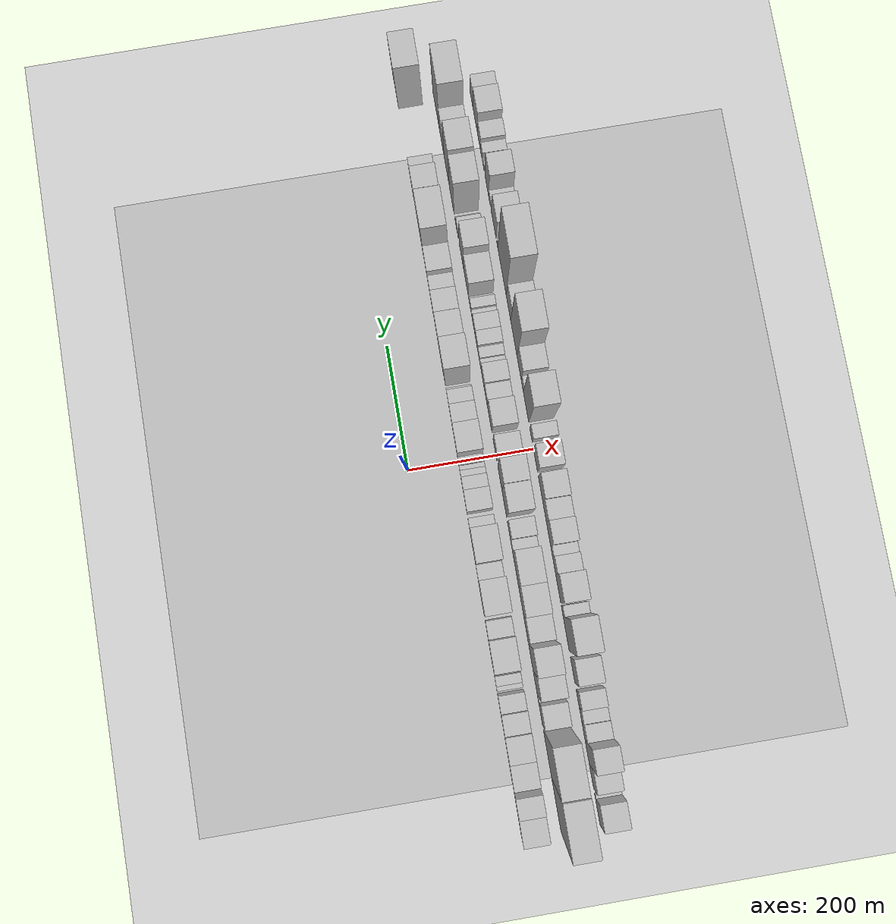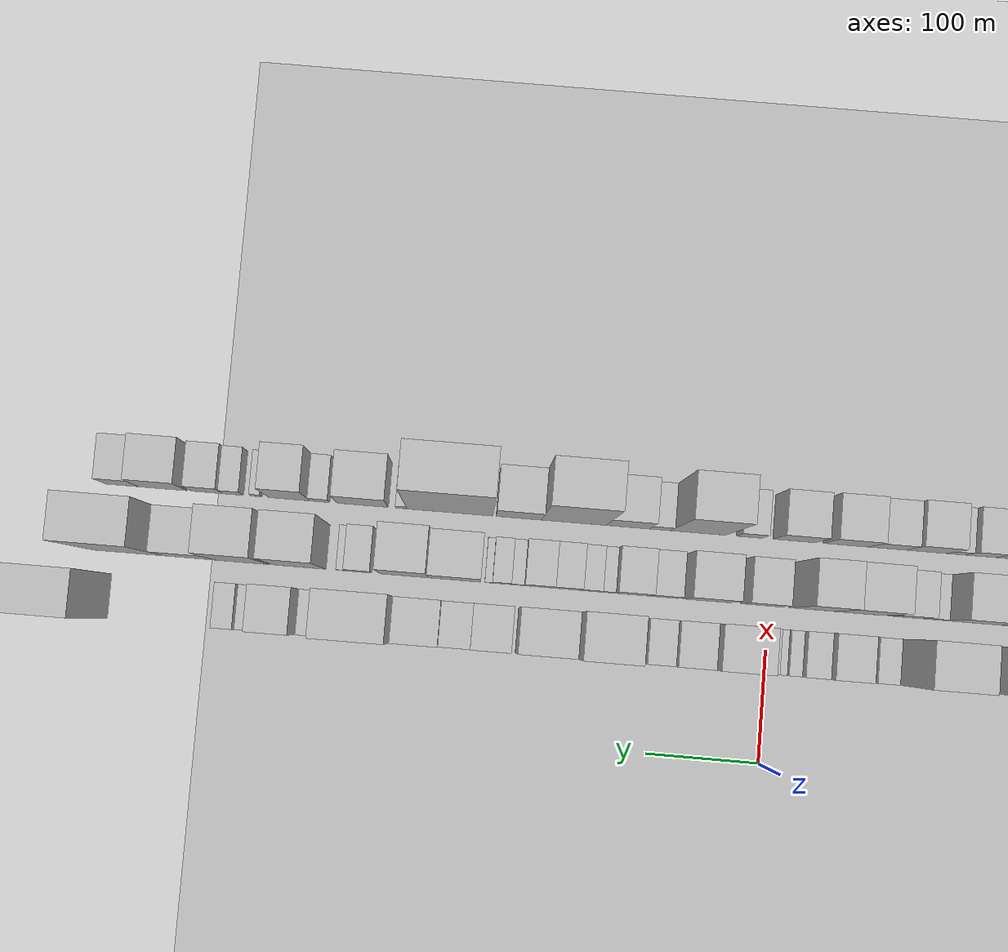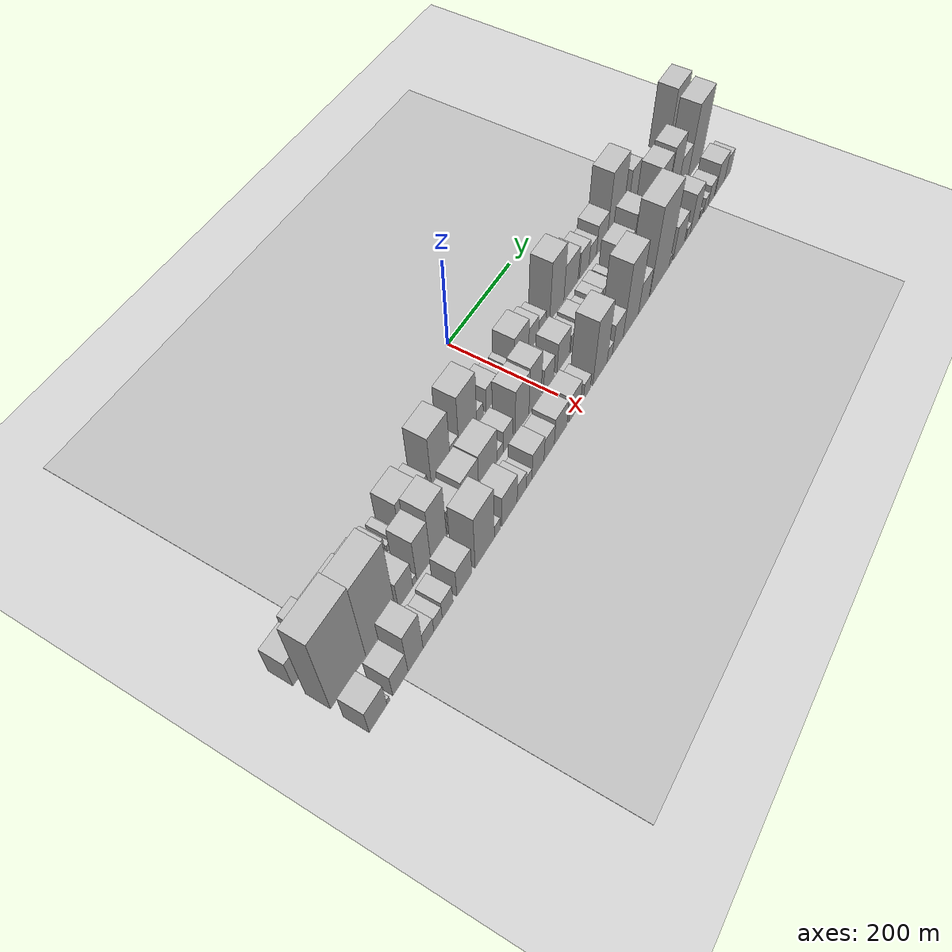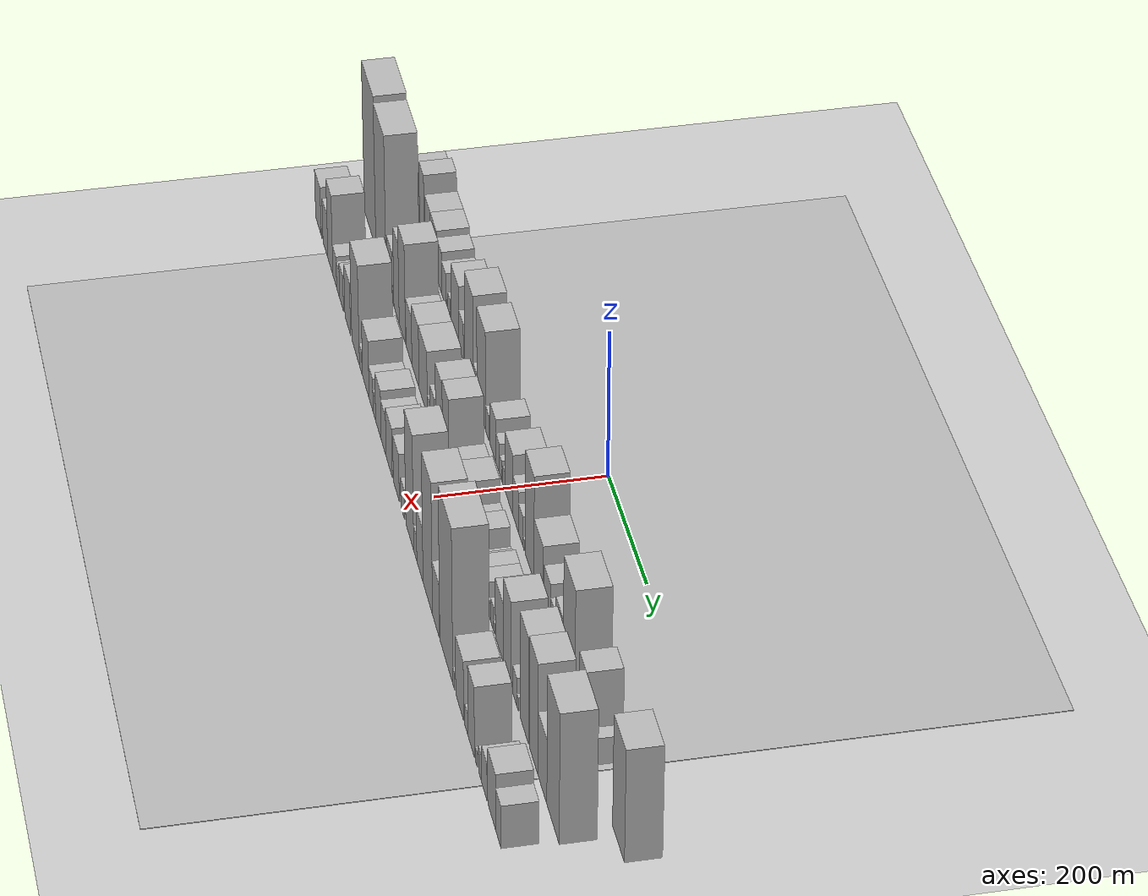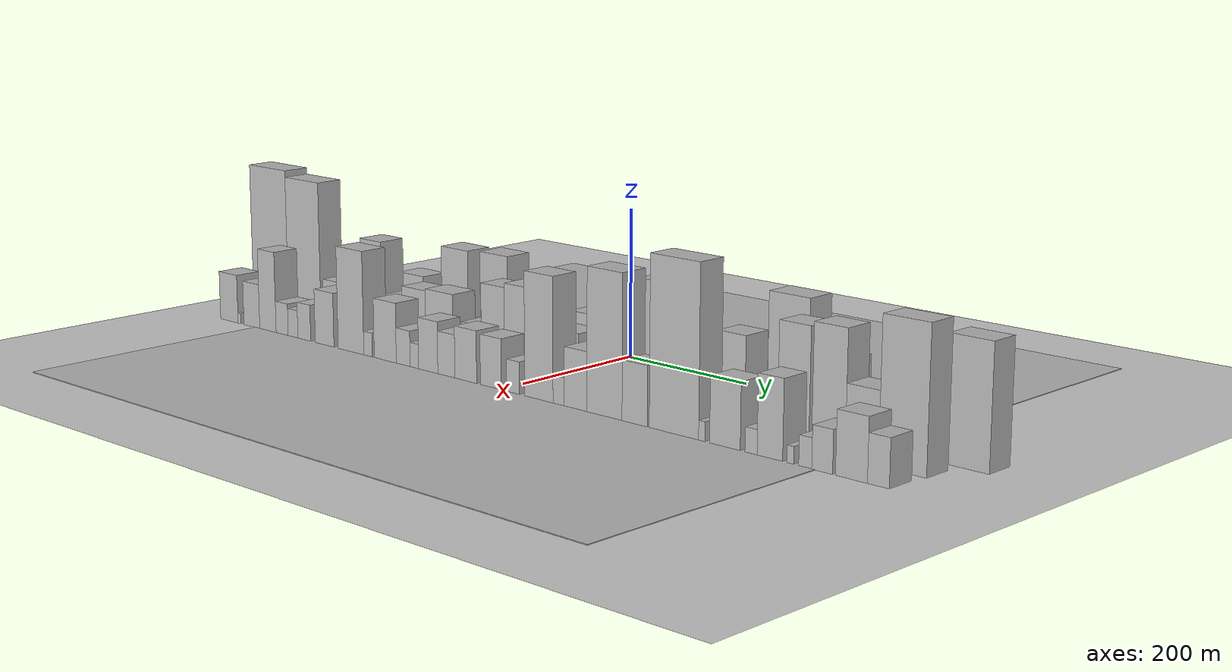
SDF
<?xml version="1.0" encoding="utf-8"?>

<sdf version="1.6">

   <world name="default">

      <gui fullscreen="0">

         <camera name="user_camera">

            <pose>-15 0 4.57585 0 0 0</pose>

            <view_controller>orbit</view_controller>

         </camera>

      </gui>

      <scene>

         <sky>

           <clouds>

             <speed>12</speed>

           </clouds>

         </sky>

         <ambient>0.4 0.4 0.4 1</ambient>

         <background>0.7 0.7 0.7 1</background>

         <shadows>1</shadows>

      </scene>

      <gravity>0 0 -9.8066</gravity>

      <magnetic_field>6e-06 2.3e-05 -4.2e-05</magnetic_field>

      <physics default="0" name="default_physics" type="ode">

         <ode>

            <solver>

               <type>quick</type>

               <iters>10</iters>

               <sor>1.0</sor>

               <use_dynamic_moi_rescaling>0</use_dynamic_moi_rescaling>

            </solver>

            <constraints>

               <cfm>0</cfm>

               <erp>0.2</erp>

               <contact_max_correcting_vel>100</contact_max_correcting_vel>

               <contact_surface_layer>0.001</contact_surface_layer>

            </constraints>

         </ode>

         <max_step_size>0.004</max_step_size>

         <real_time_factor>1</real_time_factor>

         <real_time_update_rate>250</real_time_update_rate>

      </physics>

      <light name="sun" type="directional">

         <cast_shadows>1</cast_shadows>

         <pose>0 0 10 0 0 0</pose>

         <diffuse>0.8 0.8 0.8 1</diffuse>

         <specular>0.2 0.2 0.2 1</specular>

         <attenuation>

            <range>1000</range>

            <constant>0.9</constant>

            <linear>0.01</linear>

            <quadratic>0.001</quadratic>

         </attenuation>

         <direction>-0.5 0.1 -0.9</direction>

      </light>

      <include>

         <name>ground_plane_1</name>

         <uri>model://HANNAS_ground_plane</uri>

         <pose>0 0 0  0 0 0</pose>

      </include>

      <include>

         <name>ground_plane_2</name>

         <uri>model://HANNAS_ground_plane</uri>

         <pose>100 0 0  0 0 0</pose>

      </include>

      <model name="building_1">

         <static>1</static>

         <pose frame="">100.0000 -558.4412 0 0.000000 0.000000 0.000000</pose>

         <link name="link">

            <pose frame="">0 0 37.50 0 0 0</pose>

            <collision name="collision">

               <geometry>

                  <box>

                     <size>40.0000 43.1176 75.0000</size>

                  </box>

               </geometry>

               <max_contacts>10</max_contacts>

               <surface>

                  <contact>

                     <ode/>

                  </contact>

                  <bounce/>

                  <friction>

                     <torsional>

                        <ode/>

                     </torsional>

                     <ode/>

                  </friction>

               </surface>

            </collision>

            <visual name="visual">

               <cast_shadows>0</cast_shadows>

               <geometry>

                  <box>

                     <size>40.0000 43.1176 75.0000</size>

                  </box>

               </geometry>

               <material>

                  <script>

                     <uri>model://HANNAS_wall/materials/scripts</uri>

                     <uri>model://HANNAS_wall/materials/textures</uri>

                     <name>vrc/HANNAS_wall</name>

                  </script>

               </material>

            </visual>

            <self_collide>0</self_collide>

            <enable_wind>0</enable_wind>

            <kinematic>0</kinematic>

         </link>

      </model>

      <model name="building_2">

         <static>1</static>

         <pose frame="">100.0000 -521.2993 0 0.000000 0.000000 0.000000</pose>

         <link name="link">

            <pose frame="">0 0 46.50 0 0 0</pose>

            <collision name="collision">

               <geometry>

                  <box>

                     <size>40.0000 31.1662 93.0000</size>

                  </box>

               </geometry>

               <max_contacts>10</max_contacts>

               <surface>

                  <contact>

                     <ode/>

                  </contact>

                  <bounce/>

                  <friction>

                     <torsional>

                        <ode/>

                     </torsional>

                     <ode/>

                  </friction>

               </surface>

            </collision>

            <visual name="visual">

               <cast_shadows>0</cast_shadows>

               <geometry>

                  <box>

                     <size>40.0000 31.1662 93.0000</size>

                  </box>

               </geometry>

               <material>

                  <script>

                     <uri>model://HANNAS_wall/materials/scripts</uri>

                     <uri>model://HANNAS_wall/materials/textures</uri>

                     <name>vrc/HANNAS_wall</name>

                  </script>

               </material>

            </visual>

            <self_collide>0</self_collide>

            <enable_wind>0</enable_wind>

            <kinematic>0</kinematic>

         </link>

      </model>

      <model name="building_3">

         <static>1</static>

         <pose frame="">100.0000 -481.5206 0 0.000000 0.000000 0.000000</pose>

         <link name="link">

            <pose frame="">0 0 34.50 0 0 0</pose>

            <collision name="collision">

               <geometry>

                  <box>

                     <size>40.0000 38.3912 69.0000</size>

                  </box>

               </geometry>

               <max_contacts>10</max_contacts>

               <surface>

                  <contact>

                     <ode/>

                  </contact>

                  <bounce/>

                  <friction>

                     <torsional>

                        <ode/>

                     </torsional>

                     <ode/>

                  </friction>

               </surface>

            </collision>

            <visual name="visual">

               <cast_shadows>0</cast_shadows>

               <geometry>

                  <box>

                     <size>40.0000 38.3912 69.0000</size>

                  </box>

               </geometry>

               <material>

                  <script>

                     <uri>model://HANNAS_wall/materials/scripts</uri>

                     <uri>model://HANNAS_wall/materials/textures</uri>

                     <name>vrc/HANNAS_wall</name>

                  </script>

               </material>

            </visual>

            <self_collide>0</self_collide>

            <enable_wind>0</enable_wind>

            <kinematic>0</kinematic>

         </link>

      </model>

      <model name="building_4">

         <static>1</static>

         <pose frame="">100.0000 -441.9501 0 0.000000 0.000000 0.000000</pose>

         <link name="link">

            <pose frame="">0 0 34.50 0 0 0</pose>

            <collision name="collision">

               <geometry>

                  <box>

                     <size>40.0000 40.7497 69.0000</size>

                  </box>

               </geometry>

               <max_contacts>10</max_contacts>

               <surface>

                  <contact>

                     <ode/>

                  </contact>

                  <bounce/>

                  <friction>

                     <torsional>

                        <ode/>

                     </torsional>

                     <ode/>

                  </friction>

               </surface>

            </collision>

            <visual name="visual">

               <cast_shadows>0</cast_shadows>

               <geometry>

                  <box>

                     <size>40.0000 40.7497 69.0000</size>

                  </box>

               </geometry>

               <material>

                  <script>

                     <uri>model://HANNAS_wall/materials/scripts</uri>

                     <uri>model://HANNAS_wall/materials/textures</uri>

                     <name>vrc/HANNAS_wall</name>

                  </script>

               </material>

            </visual>

            <self_collide>0</self_collide>

            <enable_wind>0</enable_wind>

            <kinematic>0</kinematic>

         </link>

      </model>

      <model name="building_5">

         <static>1</static>

         <pose frame="">100.0000 -405.6508 0 0.000000 0.000000 0.000000</pose>

         <link name="link">

            <pose frame="">0 0 30.00 0 0 0</pose>

            <collision name="collision">

               <geometry>

                  <box>

                     <size>40.0000 31.8488 60.0000</size>

                  </box>

               </geometry>

               <max_contacts>10</max_contacts>

               <surface>

                  <contact>

                     <ode/>

                  </contact>

                  <bounce/>

                  <friction>

                     <torsional>

                        <ode/>

                     </torsional>

                     <ode/>

                  </friction>

               </surface>

            </collision>

            <visual name="visual">

               <cast_shadows>0</cast_shadows>

               <geometry>

                  <box>

                     <size>40.0000 31.8488 60.0000</size>

                  </box>

               </geometry>

               <material>

                  <script>

                     <uri>model://HANNAS_wall/materials/scripts</uri>

                     <uri>model://HANNAS_wall/materials/textures</uri>

                     <name>vrc/HANNAS_wall</name>

                  </script>

               </material>

            </visual>

            <self_collide>0</self_collide>

            <enable_wind>0</enable_wind>

            <kinematic>0</kinematic>

         </link>

      </model>

      <model name="building_6">

         <static>1</static>

         <pose frame="">100.0000 -376.0400 0 0.000000 0.000000 0.000000</pose>

         <link name="link">

            <pose frame="">0 0 24.00 0 0 0</pose>

            <collision name="collision">

               <geometry>

                  <box>

                     <size>40.0000 27.3728 48.0000</size>

                  </box>

               </geometry>

               <max_contacts>10</max_contacts>

               <surface>

                  <contact>

                     <ode/>

                  </contact>

                  <bounce/>

                  <friction>

                     <torsional>

                        <ode/>

                     </torsional>

                     <ode/>

                  </friction>

               </surface>

            </collision>

            <visual name="visual">

               <cast_shadows>0</cast_shadows>

               <geometry>

                  <box>

                     <size>40.0000 27.3728 48.0000</size>

                  </box>

               </geometry>

               <material>

                  <script>

                     <uri>model://HANNAS_wall/materials/scripts</uri>

                     <uri>model://HANNAS_wall/materials/textures</uri>

                     <name>vrc/HANNAS_wall</name>

                  </script>

               </material>

            </visual>

            <self_collide>0</self_collide>

            <enable_wind>0</enable_wind>

            <kinematic>0</kinematic>

         </link>

      </model>

      <model name="building_7">

         <static>1</static>

         <pose frame="">100.0000 -354.0988 0 0.000000 0.000000 0.000000</pose>

         <link name="link">

            <pose frame="">0 0 9.00 0 0 0</pose>

            <collision name="collision">

               <geometry>

                  <box>

                     <size>40.0000 8.5097 18.0000</size>

                  </box>

               </geometry>

               <max_contacts>10</max_contacts>

               <surface>

                  <contact>

                     <ode/>

                  </contact>

                  <bounce/>

                  <friction>

                     <torsional>

                        <ode/>

                     </torsional>

                     <ode/>

                  </friction>

               </surface>

            </collision>

            <visual name="visual">

               <cast_shadows>0</cast_shadows>

               <geometry>

                  <box>

                     <size>40.0000 8.5097 18.0000</size>

                  </box>

               </geometry>

               <material>

                  <script>

                     <uri>model://HANNAS_wall/materials/scripts</uri>

                     <uri>model://HANNAS_wall/materials/textures</uri>

                     <name>vrc/HANNAS_wall</name>

                  </script>

               </material>

            </visual>

            <self_collide>0</self_collide>

            <enable_wind>0</enable_wind>

            <kinematic>0</kinematic>

         </link>

      </model>

      <model name="building_8">

         <static>1</static>

         <pose frame="">100.0000 -342.2003 0 0.000000 0.000000 0.000000</pose>

         <link name="link">

            <pose frame="">0 0 15.00 0 0 0</pose>

            <collision name="collision">

               <geometry>

                  <box>

                     <size>40.0000 15.2872 30.0000</size>

                  </box>

               </geometry>

               <max_contacts>10</max_contacts>

               <surface>

                  <contact>

                     <ode/>

                  </contact>

                  <bounce/>

                  <friction>

                     <torsional>

                        <ode/>

                     </torsional>

                     <ode/>

                  </friction>

               </surface>

            </collision>

            <visual name="visual">

               <cast_shadows>0</cast_shadows>

               <geometry>

                  <box>

                     <size>40.0000 15.2872 30.0000</size>

                  </box>

               </geometry>

               <material>

                  <script>

                     <uri>model://HANNAS_wall/materials/scripts</uri>

                     <uri>model://HANNAS_wall/materials/textures</uri>

                     <name>vrc/HANNAS_wall</name>

                  </script>

               </material>

            </visual>

            <self_collide>0</self_collide>

            <enable_wind>0</enable_wind>

            <kinematic>0</kinematic>

         </link>

      </model>

      <model name="building_9">

         <static>1</static>

         <pose frame="">100.0000 -331.0780 0 0.000000 0.000000 0.000000</pose>

         <link name="link">

            <pose frame="">0 0 7.50 0 0 0</pose>

            <collision name="collision">

               <geometry>

                  <box>

                     <size>40.0000 6.9574 15.0000</size>

                  </box>

               </geometry>

               <max_contacts>10</max_contacts>

               <surface>

                  <contact>

                     <ode/>

                  </contact>

                  <bounce/>

                  <friction>

                     <torsional>

                        <ode/>

                     </torsional>

                     <ode/>

                  </friction>

               </surface>

            </collision>

            <visual name="visual">

               <cast_shadows>0</cast_shadows>

               <geometry>

                  <box>

                     <size>40.0000 6.9574 15.0000</size>

                  </box>

               </geometry>

               <material>

                  <script>

                     <uri>model://HANNAS_wall/materials/scripts</uri>

                     <uri>model://HANNAS_wall/materials/textures</uri>

                     <name>vrc/HANNAS_wall</name>

                  </script>

               </material>

            </visual>

            <self_collide>0</self_collide>

            <enable_wind>0</enable_wind>

            <kinematic>0</kinematic>

         </link>

      </model>

      <model name="building_10">

         <static>1</static>

         <pose frame="">100.0000 -302.8728 0 0.000000 0.000000 0.000000</pose>

         <link name="link">

            <pose frame="">0 0 43.50 0 0 0</pose>

            <collision name="collision">

               <geometry>

                  <box>

                     <size>40.0000 49.4530 87.0000</size>

                  </box>

               </geometry>

               <max_contacts>10</max_contacts>

               <surface>

                  <contact>

                     <ode/>

                  </contact>

                  <bounce/>

                  <friction>

                     <torsional>

                        <ode/>

                     </torsional>

                     <ode/>

                  </friction>

               </surface>

            </collision>

            <visual name="visual">

               <cast_shadows>0</cast_shadows>

               <geometry>

                  <box>

                     <size>40.0000 49.4530 87.0000</size>

                  </box>

               </geometry>

               <material>

                  <script>

                     <uri>model://HANNAS_wall/materials/scripts</uri>

                     <uri>model://HANNAS_wall/materials/textures</uri>

                     <name>vrc/HANNAS_wall</name>

                  </script>

               </material>

            </visual>

            <self_collide>0</self_collide>

            <enable_wind>0</enable_wind>

            <kinematic>0</kinematic>

         </link>

      </model>

      <model name="building_11">

         <static>1</static>

         <pose frame="">100.0000 -263.9898 0 0.000000 0.000000 0.000000</pose>

         <link name="link">

            <pose frame="">0 0 27.00 0 0 0</pose>

            <collision name="collision">

               <geometry>

                  <box>

                     <size>40.0000 28.3131 54.0000</size>

                  </box>

               </geometry>

               <max_contacts>10</max_contacts>

               <surface>

                  <contact>

                     <ode/>

                  </contact>

                  <bounce/>

                  <friction>

                     <torsional>

                        <ode/>

                     </torsional>

                     <ode/>

                  </friction>

               </surface>

            </collision>

            <visual name="visual">

               <cast_shadows>0</cast_shadows>

               <geometry>

                  <box>

                     <size>40.0000 28.3131 54.0000</size>

                  </box>

               </geometry>

               <material>

                  <script>

                     <uri>model://HANNAS_wall/materials/scripts</uri>

                     <uri>model://HANNAS_wall/materials/textures</uri>

                     <name>vrc/HANNAS_wall</name>

                  </script>

               </material>

            </visual>

            <self_collide>0</self_collide>

            <enable_wind>0</enable_wind>

            <kinematic>0</kinematic>

         </link>

      </model>

      <model name="building_12">

         <static>1</static>

         <pose frame="">100.0000 -214.7420 0 0.000000 0.000000 0.000000</pose>

         <link name="link">

            <pose frame="">0 0 67.50 0 0 0</pose>

            <collision name="collision">

               <geometry>

                  <box>

                     <size>40.0000 52.1824 135.0000</size>

                  </box>

               </geometry>

               <max_contacts>10</max_contacts>

               <surface>

                  <contact>

                     <ode/>

                  </contact>

                  <bounce/>

                  <friction>

                     <torsional>

                        <ode/>

                     </torsional>

                     <ode/>

                  </friction>

               </surface>

            </collision>

            <visual name="visual">

               <cast_shadows>0</cast_shadows>

               <geometry>

                  <box>

                     <size>40.0000 52.1824 135.0000</size>

                  </box>

               </geometry>

               <material>

                  <script>

                     <uri>model://HANNAS_wall/materials/scripts</uri>

                     <uri>model://HANNAS_wall/materials/textures</uri>

                     <name>vrc/HANNAS_wall</name>

                  </script>

               </material>

            </visual>

            <self_collide>0</self_collide>

            <enable_wind>0</enable_wind>

            <kinematic>0</kinematic>

         </link>

      </model>

      <model name="building_13">

         <static>1</static>

         <pose frame="">100.0000 -176.5291 0 0.000000 0.000000 0.000000</pose>

         <link name="link">

            <pose frame="">0 0 21.00 0 0 0</pose>

            <collision name="collision">

               <geometry>

                  <box>

                     <size>40.0000 24.2435 42.0000</size>

                  </box>

               </geometry>

               <max_contacts>10</max_contacts>

               <surface>

                  <contact>

                     <ode/>

                  </contact>

                  <bounce/>

                  <friction>

                     <torsional>

                        <ode/>

                     </torsional>

                     <ode/>

                  </friction>

               </surface>

            </collision>

            <visual name="visual">

               <cast_shadows>0</cast_shadows>

               <geometry>

                  <box>

                     <size>40.0000 24.2435 42.0000</size>

                  </box>

               </geometry>

               <material>

                  <script>

                     <uri>model://HANNAS_wall/materials/scripts</uri>

                     <uri>model://HANNAS_wall/materials/textures</uri>

                     <name>vrc/HANNAS_wall</name>

                  </script>

               </material>

            </visual>

            <self_collide>0</self_collide>

            <enable_wind>0</enable_wind>

            <kinematic>0</kinematic>

         </link>

      </model>

      <model name="building_14">

         <static>1</static>

         <pose frame="">100.0000 -138.0995 0 0.000000 0.000000 0.000000</pose>

         <link name="link">

            <pose frame="">0 0 69.00 0 0 0</pose>

            <collision name="collision">

               <geometry>

                  <box>

                     <size>40.0000 52.6157 138.0000</size>

                  </box>

               </geometry>

               <max_contacts>10</max_contacts>

               <surface>

                  <contact>

                     <ode/>

                  </contact>

                  <bounce/>

                  <friction>

                     <torsional>

                        <ode/>

                     </torsional>

                     <ode/>

                  </friction>

               </surface>

            </collision>

            <visual name="visual">

               <cast_shadows>0</cast_shadows>

               <geometry>

                  <box>

                     <size>40.0000 52.6157 138.0000</size>

                  </box>

               </geometry>

               <material>

                  <script>

                     <uri>model://HANNAS_wall/materials/scripts</uri>

                     <uri>model://HANNAS_wall/materials/textures</uri>

                     <name>vrc/HANNAS_wall</name>

                  </script>

               </material>

            </visual>

            <self_collide>0</self_collide>

            <enable_wind>0</enable_wind>

            <kinematic>0</kinematic>

         </link>

      </model>

      <model name="building_15">

         <static>1</static>

         <pose frame="">100.0000 -102.0378 0 0.000000 0.000000 0.000000</pose>

         <link name="link">

            <pose frame="">0 0 18.00 0 0 0</pose>

            <collision name="collision">

               <geometry>

                  <box>

                     <size>40.0000 19.5076 36.0000</size>

                  </box>

               </geometry>

               <max_contacts>10</max_contacts>

               <surface>

                  <contact>

                     <ode/>

                  </contact>

                  <bounce/>

                  <friction>

                     <torsional>

                        <ode/>

                     </torsional>

                     <ode/>

                  </friction>

               </surface>

            </collision>

            <visual name="visual">

               <cast_shadows>0</cast_shadows>

               <geometry>

                  <box>

                     <size>40.0000 19.5076 36.0000</size>

                  </box>

               </geometry>

               <material>

                  <script>

                     <uri>model://HANNAS_wall/materials/scripts</uri>

                     <uri>model://HANNAS_wall/materials/textures</uri>

                     <name>vrc/HANNAS_wall</name>

                  </script>

               </material>

            </visual>

            <self_collide>0</self_collide>

            <enable_wind>0</enable_wind>

            <kinematic>0</kinematic>

         </link>

      </model>

      <model name="building_16">

         <static>1</static>

         <pose frame="">100.0000 -67.3096 0 0.000000 0.000000 0.000000</pose>

         <link name="link">

            <pose frame="">0 0 30.00 0 0 0</pose>

            <collision name="collision">

               <geometry>

                  <box>

                     <size>40.0000 33.9488 60.0000</size>

                  </box>

               </geometry>

               <max_contacts>10</max_contacts>

               <surface>

                  <contact>

                     <ode/>

                  </contact>

                  <bounce/>

                  <friction>

                     <torsional>

                        <ode/>

                     </torsional>

                     <ode/>

                  </friction>

               </surface>

            </collision>

            <visual name="visual">

               <cast_shadows>0</cast_shadows>

               <geometry>

                  <box>

                     <size>40.0000 33.9488 60.0000</size>

                  </box>

               </geometry>

               <material>

                  <script>

                     <uri>model://HANNAS_wall/materials/scripts</uri>

                     <uri>model://HANNAS_wall/materials/textures</uri>

                     <name>vrc/HANNAS_wall</name>

                  </script>

               </material>

            </visual>

            <self_collide>0</self_collide>

            <enable_wind>0</enable_wind>

            <kinematic>0</kinematic>

         </link>

      </model>

      <model name="building_17">

         <static>1</static>

         <pose frame="">100.0000 -39.3773 0 0.000000 0.000000 0.000000</pose>

         <link name="link">

            <pose frame="">0 0 21.00 0 0 0</pose>

            <collision name="collision">

               <geometry>

                  <box>

                     <size>40.0000 21.9160 42.0000</size>

                  </box>

               </geometry>

               <max_contacts>10</max_contacts>

               <surface>

                  <contact>

                     <ode/>

                  </contact>

                  <bounce/>

                  <friction>

                     <torsional>

                        <ode/>

                     </torsional>

                     <ode/>

                  </friction>

               </surface>

            </collision>

            <visual name="visual">

               <cast_shadows>0</cast_shadows>

               <geometry>

                  <box>

                     <size>40.0000 21.9160 42.0000</size>

                  </box>

               </geometry>

               <material>

                  <script>

                     <uri>model://HANNAS_wall/materials/scripts</uri>

                     <uri>model://HANNAS_wall/materials/textures</uri>

                     <name>vrc/HANNAS_wall</name>

                  </script>

               </material>

            </visual>

            <self_collide>0</self_collide>

            <enable_wind>0</enable_wind>

            <kinematic>0</kinematic>

         </link>

      </model>

      <model name="building_18">

         <static>1</static>

         <pose frame="">100.0000 -22.6179 0 0.000000 0.000000 0.000000</pose>

         <link name="link">

            <pose frame="">0 0 13.50 0 0 0</pose>

            <collision name="collision">

               <geometry>

                  <box>

                     <size>40.0000 11.6028 27.0000</size>

                  </box>

               </geometry>

               <max_contacts>10</max_contacts>

               <surface>

                  <contact>

                     <ode/>

                  </contact>

                  <bounce/>

                  <friction>

                     <torsional>

                        <ode/>

                     </torsional>

                     <ode/>

                  </friction>

               </surface>

            </collision>

            <visual name="visual">

               <cast_shadows>0</cast_shadows>

               <geometry>

                  <box>

                     <size>40.0000 11.6028 27.0000</size>

                  </box>

               </geometry>

               <material>

                  <script>

                     <uri>model://HANNAS_wall/materials/scripts</uri>

                     <uri>model://HANNAS_wall/materials/textures</uri>

                     <name>vrc/HANNAS_wall</name>

                  </script>

               </material>

            </visual>

            <self_collide>0</self_collide>

            <enable_wind>0</enable_wind>

            <kinematic>0</kinematic>

         </link>

      </model>

      <model name="building_19">

         <static>1</static>

         <pose frame="">100.0000 -12.7215 0 0.000000 0.000000 0.000000</pose>

         <link name="link">

            <pose frame="">0 0 9.00 0 0 0</pose>

            <collision name="collision">

               <geometry>

                  <box>

                     <size>40.0000 8.1899 18.0000</size>

                  </box>

               </geometry>

               <max_contacts>10</max_contacts>

               <surface>

                  <contact>

                     <ode/>

                  </contact>

                  <bounce/>

                  <friction>

                     <torsional>

                        <ode/>

                     </torsional>

                     <ode/>

                  </friction>

               </surface>

            </collision>

            <visual name="visual">

               <cast_shadows>0</cast_shadows>

               <geometry>

                  <box>

                     <size>40.0000 8.1899 18.0000</size>

                  </box>

               </geometry>

               <material>

                  <script>

                     <uri>model://HANNAS_wall/materials/scripts</uri>

                     <uri>model://HANNAS_wall/materials/textures</uri>

                     <name>vrc/HANNAS_wall</name>

                  </script>

               </material>

            </visual>

            <self_collide>0</self_collide>

            <enable_wind>0</enable_wind>

            <kinematic>0</kinematic>

         </link>

      </model>

      <model name="building_20">

         <static>1</static>

         <pose frame="">100.0000 -2.1696 0 0.000000 0.000000 0.000000</pose>

         <link name="link">

            <pose frame="">0 0 13.50 0 0 0</pose>

            <collision name="collision">

               <geometry>

                  <box>

                     <size>40.0000 12.9139 27.0000</size>

                  </box>

               </geometry>

               <max_contacts>10</max_contacts>

               <surface>

                  <contact>

                     <ode/>

                  </contact>

                  <bounce/>

                  <friction>

                     <torsional>

                        <ode/>

                     </torsional>

                     <ode/>

                  </friction>

               </surface>

            </collision>

            <visual name="visual">

               <cast_shadows>0</cast_shadows>

               <geometry>

                  <box>

                     <size>40.0000 12.9139 27.0000</size>

                  </box>

               </geometry>

               <material>

                  <script>

                     <uri>model://HANNAS_wall/materials/scripts</uri>

                     <uri>model://HANNAS_wall/materials/textures</uri>

                     <name>vrc/HANNAS_wall</name>

                  </script>

               </material>

            </visual>

            <self_collide>0</self_collide>

            <enable_wind>0</enable_wind>

            <kinematic>0</kinematic>

         </link>

      </model>

      <model name="building_21">

         <static>1</static>

         <pose frame="">100.0000 27.5766 0 0.000000 0.000000 0.000000</pose>

         <link name="link">

            <pose frame="">0 0 42.00 0 0 0</pose>

            <collision name="collision">

               <geometry>

                  <box>

                     <size>40.0000 46.5783 84.0000</size>

                  </box>

               </geometry>

               <max_contacts>10</max_contacts>

               <surface>

                  <contact>

                     <ode/>

                  </contact>

                  <bounce/>

                  <friction>

                     <torsional>

                        <ode/>

                     </torsional>

                     <ode/>

                  </friction>

               </surface>

            </collision>

            <visual name="visual">

               <cast_shadows>0</cast_shadows>

               <geometry>

                  <box>

                     <size>40.0000 46.5783 84.0000</size>

                  </box>

               </geometry>

               <material>

                  <script>

                     <uri>model://HANNAS_wall/materials/scripts</uri>

                     <uri>model://HANNAS_wall/materials/textures</uri>

                     <name>vrc/HANNAS_wall</name>

                  </script>

               </material>

            </visual>

            <self_collide>0</self_collide>

            <enable_wind>0</enable_wind>

            <kinematic>0</kinematic>

         </link>

      </model>

      <model name="building_22">

         <static>1</static>

         <pose frame="">100.0000 67.4053 0 0.000000 0.000000 0.000000</pose>

         <link name="link">

            <pose frame="">0 0 28.50 0 0 0</pose>

            <collision name="collision">

               <geometry>

                  <box>

                     <size>40.0000 33.0792 57.0000</size>

                  </box>

               </geometry>

               <max_contacts>10</max_contacts>

               <surface>

                  <contact>

                     <ode/>

                  </contact>

                  <bounce/>

                  <friction>

                     <torsional>

                        <ode/>

                     </torsional>

                     <ode/>

                  </friction>

               </surface>

            </collision>

            <visual name="visual">

               <cast_shadows>0</cast_shadows>

               <geometry>

                  <box>

                     <size>40.0000 33.0792 57.0000</size>

                  </box>

               </geometry>

               <material>

                  <script>

                     <uri>model://HANNAS_wall/materials/scripts</uri>

                     <uri>model://HANNAS_wall/materials/textures</uri>

                     <name>vrc/HANNAS_wall</name>

                  </script>

               </material>

            </visual>

            <self_collide>0</self_collide>

            <enable_wind>0</enable_wind>

            <kinematic>0</kinematic>

         </link>

      </model>

      <model name="building_23">

         <static>1</static>

         <pose frame="">100.0000 96.4477 0 0.000000 0.000000 0.000000</pose>

         <link name="link">

            <pose frame="">0 0 21.00 0 0 0</pose>

            <collision name="collision">

               <geometry>

                  <box>

                     <size>40.0000 25.0056 42.0000</size>

                  </box>

               </geometry>

               <max_contacts>10</max_contacts>

               <surface>

                  <contact>

                     <ode/>

                  </contact>

                  <bounce/>

                  <friction>

                     <torsional>

                        <ode/>

                     </torsional>

                     <ode/>

                  </friction>

               </surface>

            </collision>

            <visual name="visual">

               <cast_shadows>0</cast_shadows>

               <geometry>

                  <box>

                     <size>40.0000 25.0056 42.0000</size>

                  </box>

               </geometry>

               <material>

                  <script>

                     <uri>model://HANNAS_wall/materials/scripts</uri>

                     <uri>model://HANNAS_wall/materials/textures</uri>

                     <name>vrc/HANNAS_wall</name>

                  </script>

               </material>

            </visual>

            <self_collide>0</self_collide>

            <enable_wind>0</enable_wind>

            <kinematic>0</kinematic>

         </link>

      </model>

      <model name="building_24">

         <static>1</static>

         <pose frame="">100.0000 112.5358 0 0.000000 0.000000 0.000000</pose>

         <link name="link">

            <pose frame="">0 0 7.50 0 0 0</pose>

            <collision name="collision">

               <geometry>

                  <box>

                     <size>40.0000 7.1708 15.0000</size>

                  </box>

               </geometry>

               <max_contacts>10</max_contacts>

               <surface>

                  <contact>

                     <ode/>

                  </contact>

                  <bounce/>

                  <friction>

                     <torsional>

                        <ode/>

                     </torsional>

                     <ode/>

                  </friction>

               </surface>

            </collision>

            <visual name="visual">

               <cast_shadows>0</cast_shadows>

               <geometry>

                  <box>

                     <size>40.0000 7.1708 15.0000</size>

                  </box>

               </geometry>

               <material>

                  <script>

                     <uri>model://HANNAS_wall/materials/scripts</uri>

                     <uri>model://HANNAS_wall/materials/textures</uri>

                     <name>vrc/HANNAS_wall</name>

                  </script>

               </material>

            </visual>

            <self_collide>0</self_collide>

            <enable_wind>0</enable_wind>

            <kinematic>0</kinematic>

         </link>

      </model>

      <model name="building_25">

         <static>1</static>

         <pose frame="">100.0000 146.9329 0 0.000000 0.000000 0.000000</pose>

         <link name="link">

            <pose frame="">0 0 72.00 0 0 0</pose>

            <collision name="collision">

               <geometry>

                  <box>

                     <size>40.0000 49.6233 144.0000</size>

                  </box>

               </geometry>

               <max_contacts>10</max_contacts>

               <surface>

                  <contact>

                     <ode/>

                  </contact>

                  <bounce/>

                  <friction>

                     <torsional>

                        <ode/>

                     </torsional>

                     <ode/>

                  </friction>

               </surface>

            </collision>

            <visual name="visual">

               <cast_shadows>0</cast_shadows>

               <geometry>

                  <box>

                     <size>40.0000 49.6233 144.0000</size>

                  </box>

               </geometry>

               <material>

                  <script>

                     <uri>model://HANNAS_wall/materials/scripts</uri>

                     <uri>model://HANNAS_wall/materials/textures</uri>

                     <name>vrc/HANNAS_wall</name>

                  </script>

               </material>

            </visual>

            <self_collide>0</self_collide>

            <enable_wind>0</enable_wind>

            <kinematic>0</kinematic>

         </link>

      </model>

      <model name="building_26">

         <static>1</static>

         <pose frame="">100.0000 197.2676 0 0.000000 0.000000 0.000000</pose>

         <link name="link">

            <pose frame="">0 0 43.50 0 0 0</pose>

            <collision name="collision">

               <geometry>

                  <box>

                     <size>40.0000 51.0462 87.0000</size>

                  </box>

               </geometry>

               <max_contacts>10</max_contacts>

               <surface>

                  <contact>

                     <ode/>

                  </contact>

                  <bounce/>

                  <friction>

                     <torsional>

                        <ode/>

                     </torsional>

                     <ode/>

                  </friction>

               </surface>

            </collision>

            <visual name="visual">

               <cast_shadows>0</cast_shadows>

               <geometry>

                  <box>

                     <size>40.0000 51.0462 87.0000</size>

                  </box>

               </geometry>

               <material>

                  <script>

                     <uri>model://HANNAS_wall/materials/scripts</uri>

                     <uri>model://HANNAS_wall/materials/textures</uri>

                     <name>vrc/HANNAS_wall</name>

                  </script>

               </material>

            </visual>

            <self_collide>0</self_collide>

            <enable_wind>0</enable_wind>

            <kinematic>0</kinematic>

         </link>

      </model>

      <model name="building_27">

         <static>1</static>

         <pose frame="">100.0000 245.4375 0 0.000000 0.000000 0.000000</pose>

         <link name="link">

            <pose frame="">0 0 33.00 0 0 0</pose>

            <collision name="collision">

               <geometry>

                  <box>

                     <size>40.0000 35.2936 66.0000</size>

                  </box>

               </geometry>

               <max_contacts>10</max_contacts>

               <surface>

                  <contact>

                     <ode/>

                  </contact>

                  <bounce/>

                  <friction>

                     <torsional>

                        <ode/>

                     </torsional>

                     <ode/>

                  </friction>

               </surface>

            </collision>

            <visual name="visual">

               <cast_shadows>0</cast_shadows>

               <geometry>

                  <box>

                     <size>40.0000 35.2936 66.0000</size>

                  </box>

               </geometry>

               <material>

                  <script>

                     <uri>model://HANNAS_wall/materials/scripts</uri>

                     <uri>model://HANNAS_wall/materials/textures</uri>

                     <name>vrc/HANNAS_wall</name>

                  </script>

               </material>

            </visual>

            <self_collide>0</self_collide>

            <enable_wind>0</enable_wind>

            <kinematic>0</kinematic>

         </link>

      </model>

      <model name="building_28">

         <static>1</static>

         <pose frame="">100.0000 277.1267 0 0.000000 0.000000 0.000000</pose>

         <link name="link">

            <pose frame="">0 0 24.00 0 0 0</pose>

            <collision name="collision">

               <geometry>

                  <box>

                     <size>40.0000 28.0849 48.0000</size>

                  </box>

               </geometry>

               <max_contacts>10</max_contacts>

               <surface>

                  <contact>

                     <ode/>

                  </contact>

                  <bounce/>

                  <friction>

                     <torsional>

                        <ode/>

                     </torsional>

                     <ode/>

                  </friction>

               </surface>

            </collision>

            <visual name="visual">

               <cast_shadows>0</cast_shadows>

               <geometry>

                  <box>

                     <size>40.0000 28.0849 48.0000</size>

                  </box>

               </geometry>

               <material>

                  <script>

                     <uri>model://HANNAS_wall/materials/scripts</uri>

                     <uri>model://HANNAS_wall/materials/textures</uri>

                     <name>vrc/HANNAS_wall</name>

                  </script>

               </material>

            </visual>

            <self_collide>0</self_collide>

            <enable_wind>0</enable_wind>

            <kinematic>0</kinematic>

         </link>

      </model>

      <model name="building_29">

         <static>1</static>

         <pose frame="">100.0000 311.7803 0 0.000000 0.000000 0.000000</pose>

         <link name="link">

            <pose frame="">0 0 36.00 0 0 0</pose>

            <collision name="collision">

               <geometry>

                  <box>

                     <size>40.0000 41.2224 72.0000</size>

                  </box>

               </geometry>

               <max_contacts>10</max_contacts>

               <surface>

                  <contact>

                     <ode/>

                  </contact>

                  <bounce/>

                  <friction>

                     <torsional>

                        <ode/>

                     </torsional>

                     <ode/>

                  </friction>

               </surface>

            </collision>

            <visual name="visual">

               <cast_shadows>0</cast_shadows>

               <geometry>

                  <box>

                     <size>40.0000 41.2224 72.0000</size>

                  </box>

               </geometry>

               <material>

                  <script>

                     <uri>model://HANNAS_wall/materials/scripts</uri>

                     <uri>model://HANNAS_wall/materials/textures</uri>

                     <name>vrc/HANNAS_wall</name>

                  </script>

               </material>

            </visual>

            <self_collide>0</self_collide>

            <enable_wind>0</enable_wind>

            <kinematic>0</kinematic>

         </link>

      </model>

      <model name="building_30">

         <static>1</static>

         <pose frame="">100.0000 363.3565 0 0.000000 0.000000 0.000000</pose>

         <link name="link">

            <pose frame="">0 0 79.50 0 0 0</pose>

            <collision name="collision">

               <geometry>

                  <box>

                     <size>40.0000 61.9299 159.0000</size>

                  </box>

               </geometry>

               <max_contacts>10</max_contacts>

               <surface>

                  <contact>

                     <ode/>

                  </contact>

                  <bounce/>

                  <friction>

                     <torsional>

                        <ode/>

                     </torsional>

                     <ode/>

                  </friction>

               </surface>

            </collision>

            <visual name="visual">

               <cast_shadows>0</cast_shadows>

               <geometry>

                  <box>

                     <size>40.0000 61.9299 159.0000</size>

                  </box>

               </geometry>

               <material>

                  <script>

                     <uri>model://HANNAS_wall/materials/scripts</uri>

                     <uri>model://HANNAS_wall/materials/textures</uri>

                     <name>vrc/HANNAS_wall</name>

                  </script>

               </material>

            </visual>

            <self_collide>0</self_collide>

            <enable_wind>0</enable_wind>

            <kinematic>0</kinematic>

         </link>

      </model>

      <model name="building_31">

         <static>1</static>

         <pose frame="">100.0000 406.9446 0 0.000000 0.000000 0.000000</pose>

         <link name="link">

            <pose frame="">0 0 16.50 0 0 0</pose>

            <collision name="collision">

               <geometry>

                  <box>

                     <size>40.0000 19.2463 33.0000</size>

                  </box>

               </geometry>

               <max_contacts>10</max_contacts>

               <surface>

                  <contact>

                     <ode/>

                  </contact>

                  <bounce/>

                  <friction>

                     <torsional>

                        <ode/>

                     </torsional>

                     <ode/>

                  </friction>

               </surface>

            </collision>

            <visual name="visual">

               <cast_shadows>0</cast_shadows>

               <geometry>

                  <box>

                     <size>40.0000 19.2463 33.0000</size>

                  </box>

               </geometry>

               <material>

                  <script>

                     <uri>model://HANNAS_wall/materials/scripts</uri>

                     <uri>model://HANNAS_wall/materials/textures</uri>

                     <name>vrc/HANNAS_wall</name>

                  </script>

               </material>

            </visual>

            <self_collide>0</self_collide>

            <enable_wind>0</enable_wind>

            <kinematic>0</kinematic>

         </link>

      </model>

      <model name="building_32">

         <static>1</static>

         <pose frame="">100.0000 435.1259 0 0.000000 0.000000 0.000000</pose>

         <link name="link">

            <pose frame="">0 0 48.00 0 0 0</pose>

            <collision name="collision">

               <geometry>

                  <box>

                     <size>40.0000 37.1163 96.0000</size>

                  </box>

               </geometry>

               <max_contacts>10</max_contacts>

               <surface>

                  <contact>

                     <ode/>

                  </contact>

                  <bounce/>

                  <friction>

                     <torsional>

                        <ode/>

                     </torsional>

                     <ode/>

                  </friction>

               </surface>

            </collision>

            <visual name="visual">

               <cast_shadows>0</cast_shadows>

               <geometry>

                  <box>

                     <size>40.0000 37.1163 96.0000</size>

                  </box>

               </geometry>

               <material>

                  <script>

                     <uri>model://HANNAS_wall/materials/scripts</uri>

                     <uri>model://HANNAS_wall/materials/textures</uri>

                     <name>vrc/HANNAS_wall</name>

                  </script>

               </material>

            </visual>

            <self_collide>0</self_collide>

            <enable_wind>0</enable_wind>

            <kinematic>0</kinematic>

         </link>

      </model>

      <model name="building_33">

         <static>1</static>

         <pose frame="">100.0000 458.2078 0 0.000000 0.000000 0.000000</pose>

         <link name="link">

            <pose frame="">0 0 10.50 0 0 0</pose>

            <collision name="collision">

               <geometry>

                  <box>

                     <size>40.0000 9.0475 21.0000</size>

                  </box>

               </geometry>

               <max_contacts>10</max_contacts>

               <surface>

                  <contact>

                     <ode/>

                  </contact>

                  <bounce/>

                  <friction>

                     <torsional>

                        <ode/>

                     </torsional>

                     <ode/>

                  </friction>

               </surface>

            </collision>

            <visual name="visual">

               <cast_shadows>0</cast_shadows>

               <geometry>

                  <box>

                     <size>40.0000 9.0475 21.0000</size>

                  </box>

               </geometry>

               <material>

                  <script>

                     <uri>model://HANNAS_wall/materials/scripts</uri>

                     <uri>model://HANNAS_wall/materials/textures</uri>

                     <name>vrc/HANNAS_wall</name>

                  </script>

               </material>

            </visual>

            <self_collide>0</self_collide>

            <enable_wind>0</enable_wind>

            <kinematic>0</kinematic>

         </link>

      </model>

      <model name="building_34">

         <static>1</static>

         <pose frame="">100.0000 467.2337 0 0.000000 0.000000 0.000000</pose>

         <link name="link">

            <pose frame="">0 0 10.50 0 0 0</pose>

            <collision name="collision">

               <geometry>

                  <box>

                     <size>40.0000 9.0043 21.0000</size>

                  </box>

               </geometry>

               <max_contacts>10</max_contacts>

               <surface>

                  <contact>

                     <ode/>

                  </contact>

                  <bounce/>

                  <friction>

                     <torsional>

                        <ode/>

                     </torsional>

                     <ode/>

                  </friction>

               </surface>

            </collision>

            <visual name="visual">

               <cast_shadows>0</cast_shadows>

               <geometry>

                  <box>

                     <size>40.0000 9.0043 21.0000</size>

                  </box>

               </geometry>

               <material>

                  <script>

                     <uri>model://HANNAS_wall/materials/scripts</uri>

                     <uri>model://HANNAS_wall/materials/textures</uri>

                     <name>vrc/HANNAS_wall</name>

                  </script>

               </material>

            </visual>

            <self_collide>0</self_collide>

            <enable_wind>0</enable_wind>

            <kinematic>0</kinematic>

         </link>

      </model>

      <model name="building_35">

         <static>1</static>

         <pose frame="">100.0000 481.1040 0 0.000000 0.000000 0.000000</pose>

         <link name="link">

            <pose frame="">0 0 18.00 0 0 0</pose>

            <collision name="collision">

               <geometry>

                  <box>

                     <size>40.0000 18.7363 36.0000</size>

                  </box>

               </geometry>

               <max_contacts>10</max_contacts>

               <surface>

                  <contact>

                     <ode/>

                  </contact>

                  <bounce/>

                  <friction>

                     <torsional>

                        <ode/>

                     </torsional>

                     <ode/>

                  </friction>

               </surface>

            </collision>

            <visual name="visual">

               <cast_shadows>0</cast_shadows>

               <geometry>

                  <box>

                     <size>40.0000 18.7363 36.0000</size>

                  </box>

               </geometry>

               <material>

                  <script>

                     <uri>model://HANNAS_wall/materials/scripts</uri>

                     <uri>model://HANNAS_wall/materials/textures</uri>

                     <name>vrc/HANNAS_wall</name>

                  </script>

               </material>

            </visual>

            <self_collide>0</self_collide>

            <enable_wind>0</enable_wind>

            <kinematic>0</kinematic>

         </link>

      </model>

      <model name="building_36">

         <static>1</static>

         <pose frame="">100.0000 617.7021 0 0.000000 0.000000 0.000000</pose>

         <link name="link">

            <pose frame="">0 0 75.00 0 0 0</pose>

            <collision name="collision">

               <geometry>

                  <box>

                     <size>40.0000 58.8200 150.0000</size>

                  </box>

               </geometry>

               <max_contacts>10</max_contacts>

               <surface>

                  <contact>

                     <ode/>

                  </contact>

                  <bounce/>

                  <friction>

                     <torsional>

                        <ode/>

                     </torsional>

                     <ode/>

                  </friction>

               </surface>

            </collision>

            <visual name="visual">

               <cast_shadows>0</cast_shadows>

               <geometry>

                  <box>

                     <size>40.0000 58.8200 150.0000</size>

                  </box>

               </geometry>

               <material>

                  <script>

                     <uri>model://HANNAS_wall/materials/scripts</uri>

                     <uri>model://HANNAS_wall/materials/textures</uri>

                     <name>vrc/HANNAS_wall</name>

                  </script>

               </material>

            </visual>

            <self_collide>0</self_collide>

            <enable_wind>0</enable_wind>

            <kinematic>0</kinematic>

         </link>

      </model>

      <model name="building_37">

         <static>1</static>

         <pose frame="">160.0000 -539.8047 0 0.000000 0.000000 0.000000</pose>

         <link name="link">

            <pose frame="">0 0 108.00 0 0 0</pose>

            <collision name="collision">

               <geometry>

                  <box>

                     <size>40.0000 80.3907 216.0000</size>

                  </box>

               </geometry>

               <max_contacts>10</max_contacts>

               <surface>

                  <contact>

                     <ode/>

                  </contact>

                  <bounce/>

                  <friction>

                     <torsional>

                        <ode/>

                     </torsional>

                     <ode/>

                  </friction>

               </surface>

            </collision>

            <visual name="visual">

               <cast_shadows>0</cast_shadows>

               <geometry>

                  <box>

                     <size>40.0000 80.3907 216.0000</size>

                  </box>

               </geometry>

               <material>

                  <script>

                     <uri>model://HANNAS_wall/materials/scripts</uri>

                     <uri>model://HANNAS_wall/materials/textures</uri>

                     <name>vrc/HANNAS_wall</name>

                  </script>

               </material>

            </visual>

            <self_collide>0</self_collide>

            <enable_wind>0</enable_wind>

            <kinematic>0</kinematic>

         </link>

      </model>

      <model name="building_38">

         <static>1</static>

         <pose frame="">160.0000 -463.3881 0 0.000000 0.000000 0.000000</pose>

         <link name="link">

            <pose frame="">0 0 103.50 0 0 0</pose>

            <collision name="collision">

               <geometry>

                  <box>

                     <size>40.0000 72.4423 207.0000</size>

                  </box>

               </geometry>

               <max_contacts>10</max_contacts>

               <surface>

                  <contact>

                     <ode/>

                  </contact>

                  <bounce/>

                  <friction>

                     <torsional>

                        <ode/>

                     </torsional>

                     <ode/>

                  </friction>

               </surface>

            </collision>

            <visual name="visual">

               <cast_shadows>0</cast_shadows>

               <geometry>

                  <box>

                     <size>40.0000 72.4423 207.0000</size>

                  </box>

               </geometry>

               <material>

                  <script>

                     <uri>model://HANNAS_wall/materials/scripts</uri>

                     <uri>model://HANNAS_wall/materials/textures</uri>

                     <name>vrc/HANNAS_wall</name>

                  </script>

               </material>

            </visual>

            <self_collide>0</self_collide>

            <enable_wind>0</enable_wind>

            <kinematic>0</kinematic>

         </link>

      </model>

      <model name="building_39">

         <static>1</static>

         <pose frame="">160.0000 -402.9749 0 0.000000 0.000000 0.000000</pose>

         <link name="link">

            <pose frame="">0 0 36.00 0 0 0</pose>

            <collision name="collision">

               <geometry>

                  <box>

                     <size>40.0000 36.3841 72.0000</size>

                  </box>

               </geometry>

               <max_contacts>10</max_contacts>

               <surface>

                  <contact>

                     <ode/>

                  </contact>

                  <bounce/>

                  <friction>

                     <torsional>

                        <ode/>

                     </torsional>

                     <ode/>

                  </friction>

               </surface>

            </collision>

            <visual name="visual">

               <cast_shadows>0</cast_shadows>

               <geometry>

                  <box>

                     <size>40.0000 36.3841 72.0000</size>

                  </box>

               </geometry>

               <material>

                  <script>

                     <uri>model://HANNAS_wall/materials/scripts</uri>

                     <uri>model://HANNAS_wall/materials/textures</uri>

                     <name>vrc/HANNAS_wall</name>

                  </script>

               </material>

            </visual>

            <self_collide>0</self_collide>

            <enable_wind>0</enable_wind>

            <kinematic>0</kinematic>

         </link>

      </model>

      <model name="building_40">

         <static>1</static>

         <pose frame="">160.0000 -379.8645 0 0.000000 0.000000 0.000000</pose>

         <link name="link">

            <pose frame="">0 0 10.50 0 0 0</pose>

            <collision name="collision">

               <geometry>

                  <box>

                     <size>40.0000 9.8367 21.0000</size>

                  </box>

               </geometry>

               <max_contacts>10</max_contacts>

               <surface>

                  <contact>

                     <ode/>

                  </contact>

                  <bounce/>

                  <friction>

                     <torsional>

                        <ode/>

                     </torsional>

                     <ode/>

                  </friction>

               </surface>

            </collision>

            <visual name="visual">

               <cast_shadows>0</cast_shadows>

               <geometry>

                  <box>

                     <size>40.0000 9.8367 21.0000</size>

                  </box>

               </geometry>

               <material>

                  <script>

                     <uri>model://HANNAS_wall/materials/scripts</uri>

                     <uri>model://HANNAS_wall/materials/textures</uri>

                     <name>vrc/HANNAS_wall</name>

                  </script>

               </material>

            </visual>

            <self_collide>0</self_collide>

            <enable_wind>0</enable_wind>

            <kinematic>0</kinematic>

         </link>

      </model>

      <model name="building_41">

         <static>1</static>

         <pose frame="">160.0000 -356.9535 0 0.000000 0.000000 0.000000</pose>

         <link name="link">

            <pose frame="">0 0 57.00 0 0 0</pose>

            <collision name="collision">

               <geometry>

                  <box>

                     <size>40.0000 35.9852 114.0000</size>

                  </box>

               </geometry>

               <max_contacts>10</max_contacts>

               <surface>

                  <contact>

                     <ode/>

                  </contact>

                  <bounce/>

                  <friction>

                     <torsional>

                        <ode/>

                     </torsional>

                     <ode/>

                  </friction>

               </surface>

            </collision>

            <visual name="visual">

               <cast_shadows>0</cast_shadows>

               <geometry>

                  <box>

                     <size>40.0000 35.9852 114.0000</size>

                  </box>

               </geometry>

               <material>

                  <script>

                     <uri>model://HANNAS_wall/materials/scripts</uri>

                     <uri>model://HANNAS_wall/materials/textures</uri>

                     <name>vrc/HANNAS_wall</name>

                  </script>

               </material>

            </visual>

            <self_collide>0</self_collide>

            <enable_wind>0</enable_wind>

            <kinematic>0</kinematic>

         </link>

      </model>

      <model name="building_42">

         <static>1</static>

         <pose frame="">160.0000 -317.7506 0 0.000000 0.000000 0.000000</pose>

         <link name="link">

            <pose frame="">0 0 70.50 0 0 0</pose>

            <collision name="collision">

               <geometry>

                  <box>

                     <size>40.0000 42.4207 141.0000</size>

                  </box>

               </geometry>

               <max_contacts>10</max_contacts>

               <surface>

                  <contact>

                     <ode/>

                  </contact>

                  <bounce/>

                  <friction>

                     <torsional>

                        <ode/>

                     </torsional>

                     <ode/>

                  </friction>

               </surface>

            </collision>

            <visual name="visual">

               <cast_shadows>0</cast_shadows>

               <geometry>

                  <box>

                     <size>40.0000 42.4207 141.0000</size>

                  </box>

               </geometry>

               <material>

                  <script>

                     <uri>model://HANNAS_wall/materials/scripts</uri>

                     <uri>model://HANNAS_wall/materials/textures</uri>

                     <name>vrc/HANNAS_wall</name>

                  </script>

               </material>

            </visual>

            <self_collide>0</self_collide>

            <enable_wind>0</enable_wind>

            <kinematic>0</kinematic>

         </link>

      </model>

      <model name="building_43">

         <static>1</static>

         <pose frame="">160.0000 -273.8139 0 0.000000 0.000000 0.000000</pose>

         <link name="link">

            <pose frame="">0 0 34.50 0 0 0</pose>

            <collision name="collision">

               <geometry>

                  <box>

                     <size>40.0000 39.4525 69.0000</size>

                  </box>

               </geometry>

               <max_contacts>10</max_contacts>

               <surface>

                  <contact>

                     <ode/>

                  </contact>

                  <bounce/>

                  <friction>

                     <torsional>

                        <ode/>

                     </torsional>

                     <ode/>

                  </friction>

               </surface>

            </collision>

            <visual name="visual">

               <cast_shadows>0</cast_shadows>

               <geometry>

                  <box>

                     <size>40.0000 39.4525 69.0000</size>

                  </box>

               </geometry>

               <material>

                  <script>

                     <uri>model://HANNAS_wall/materials/scripts</uri>

                     <uri>model://HANNAS_wall/materials/textures</uri>

                     <name>vrc/HANNAS_wall</name>

                  </script>

               </material>

            </visual>

            <self_collide>0</self_collide>

            <enable_wind>0</enable_wind>

            <kinematic>0</kinematic>

         </link>

      </model>

      <model name="building_44">

         <static>1</static>

         <pose frame="">160.0000 -230.6634 0 0.000000 0.000000 0.000000</pose>

         <link name="link">

            <pose frame="">0 0 43.50 0 0 0</pose>

            <collision name="collision">

               <geometry>

                  <box>

                     <size>40.0000 46.8486 87.0000</size>

                  </box>

               </geometry>

               <max_contacts>10</max_contacts>

               <surface>

                  <contact>

                     <ode/>

                  </contact>

                  <bounce/>

                  <friction>

                     <torsional>

                        <ode/>

                     </torsional>

                     <ode/>

                  </friction>

               </surface>

            </collision>

            <visual name="visual">

               <cast_shadows>0</cast_shadows>

               <geometry>

                  <box>

                     <size>40.0000 46.8486 87.0000</size>

                  </box>

               </geometry>

               <material>

                  <script>

                     <uri>model://HANNAS_wall/materials/scripts</uri>

                     <uri>model://HANNAS_wall/materials/textures</uri>

                     <name>vrc/HANNAS_wall</name>

                  </script>

               </material>

            </visual>

            <self_collide>0</self_collide>

            <enable_wind>0</enable_wind>

            <kinematic>0</kinematic>

         </link>

      </model>

      <model name="building_45">

         <static>1</static>

         <pose frame="">160.0000 -180.2933 0 0.000000 0.000000 0.000000</pose>

         <link name="link">

            <pose frame="">0 0 45.00 0 0 0</pose>

            <collision name="collision">

               <geometry>

                  <box>

                     <size>40.0000 53.8916 90.0000</size>

                  </box>

               </geometry>

               <max_contacts>10</max_contacts>

               <surface>

                  <contact>

                     <ode/>

                  </contact>

                  <bounce/>

                  <friction>

                     <torsional>

                        <ode/>

                     </torsional>

                     <ode/>

                  </friction>

               </surface>

            </collision>

            <visual name="visual">

               <cast_shadows>0</cast_shadows>

               <geometry>

                  <box>

                     <size>40.0000 53.8916 90.0000</size>

                  </box>

               </geometry>

               <material>

                  <script>

                     <uri>model://HANNAS_wall/materials/scripts</uri>

                     <uri>model://HANNAS_wall/materials/textures</uri>

                     <name>vrc/HANNAS_wall</name>

                  </script>

               </material>

            </visual>

            <self_collide>0</self_collide>

            <enable_wind>0</enable_wind>

            <kinematic>0</kinematic>

         </link>

      </model>

      <model name="building_46">

         <static>1</static>

         <pose frame="">160.0000 -144.5424 0 0.000000 0.000000 0.000000</pose>

         <link name="link">

            <pose frame="">0 0 15.00 0 0 0</pose>

            <collision name="collision">

               <geometry>

                  <box>

                     <size>40.0000 17.6103 30.0000</size>

                  </box>

               </geometry>

               <max_contacts>10</max_contacts>

               <surface>

                  <contact>

                     <ode/>

                  </contact>

                  <bounce/>

                  <friction>

                     <torsional>

                        <ode/>

                     </torsional>

                     <ode/>

                  </friction>

               </surface>

            </collision>

            <visual name="visual">

               <cast_shadows>0</cast_shadows>

               <geometry>

                  <box>

                     <size>40.0000 17.6103 30.0000</size>

                  </box>

               </geometry>

               <material>

                  <script>

                     <uri>model://HANNAS_wall/materials/scripts</uri>

                     <uri>model://HANNAS_wall/materials/textures</uri>

                     <name>vrc/HANNAS_wall</name>

                  </script>

               </material>

            </visual>

            <self_collide>0</self_collide>

            <enable_wind>0</enable_wind>

            <kinematic>0</kinematic>

         </link>

      </model>

      <model name="building_47">

         <static>1</static>

         <pose frame="">160.0000 -120.9377 0 0.000000 0.000000 0.000000</pose>

         <link name="link">

            <pose frame="">0 0 28.50 0 0 0</pose>

            <collision name="collision">

               <geometry>

                  <box>

                     <size>40.0000 29.5990 57.0000</size>

                  </box>

               </geometry>

               <max_contacts>10</max_contacts>

               <surface>

                  <contact>

                     <ode/>

                  </contact>

                  <bounce/>

                  <friction>

                     <torsional>

                        <ode/>

                     </torsional>

                     <ode/>

                  </friction>

               </surface>

            </collision>

            <visual name="visual">

               <cast_shadows>0</cast_shadows>

               <geometry>

                  <box>

                     <size>40.0000 29.5990 57.0000</size>

                  </box>

               </geometry>

               <material>

                  <script>

                     <uri>model://HANNAS_wall/materials/scripts</uri>

                     <uri>model://HANNAS_wall/materials/textures</uri>

                     <name>vrc/HANNAS_wall</name>

                  </script>

               </material>

            </visual>

            <self_collide>0</self_collide>

            <enable_wind>0</enable_wind>

            <kinematic>0</kinematic>

         </link>

      </model>

      <model name="building_48">

         <static>1</static>

         <pose frame="">160.0000 -77.5481 0 0.000000 0.000000 0.000000</pose>

         <link name="link">

            <pose frame="">0 0 57.00 0 0 0</pose>

            <collision name="collision">

               <geometry>

                  <box>

                     <size>40.0000 43.1801 114.0000</size>

                  </box>

               </geometry>

               <max_contacts>10</max_contacts>

               <surface>

                  <contact>

                     <ode/>

                  </contact>

                  <bounce/>

                  <friction>

                     <torsional>

                        <ode/>

                     </torsional>

                     <ode/>

                  </friction>

               </surface>

            </collision>

            <visual name="visual">

               <cast_shadows>0</cast_shadows>

               <geometry>

                  <box>

                     <size>40.0000 43.1801 114.0000</size>

                  </box>

               </geometry>

               <material>

                  <script>

                     <uri>model://HANNAS_wall/materials/scripts</uri>

                     <uri>model://HANNAS_wall/materials/textures</uri>

                     <name>vrc/HANNAS_wall</name>

                  </script>

               </material>

            </visual>

            <self_collide>0</self_collide>

            <enable_wind>0</enable_wind>

            <kinematic>0</kinematic>

         </link>

      </model>

      <model name="building_49">

         <static>1</static>

         <pose frame="">160.0000 -36.6136 0 0.000000 0.000000 0.000000</pose>

         <link name="link">

            <pose frame="">0 0 60.00 0 0 0</pose>

            <collision name="collision">

               <geometry>

                  <box>

                     <size>40.0000 38.6889 120.0000</size>

                  </box>

               </geometry>

               <max_contacts>10</max_contacts>

               <surface>

                  <contact>

                     <ode/>

                  </contact>

                  <bounce/>

                  <friction>

                     <torsional>

                        <ode/>

                     </torsional>

                     <ode/>

                  </friction>

               </surface>

            </collision>

            <visual name="visual">

               <cast_shadows>0</cast_shadows>

               <geometry>

                  <box>

                     <size>40.0000 38.6889 120.0000</size>

                  </box>

               </geometry>

               <material>

                  <script>

                     <uri>model://HANNAS_wall/materials/scripts</uri>

                     <uri>model://HANNAS_wall/materials/textures</uri>

                     <name>vrc/HANNAS_wall</name>

                  </script>

               </material>

            </visual>

            <self_collide>0</self_collide>

            <enable_wind>0</enable_wind>

            <kinematic>0</kinematic>

         </link>

      </model>

      <model name="building_50">

         <static>1</static>

         <pose frame="">160.0000 8.1634 0 0.000000 0.000000 0.000000</pose>

         <link name="link">

            <pose frame="">0 0 30.00 0 0 0</pose>

            <collision name="collision">

               <geometry>

                  <box>

                     <size>40.0000 34.8651 60.0000</size>

                  </box>

               </geometry>

               <max_contacts>10</max_contacts>

               <surface>

                  <contact>

                     <ode/>

                  </contact>

                  <bounce/>

                  <friction>

                     <torsional>

                        <ode/>

                     </torsional>

                     <ode/>

                  </friction>

               </surface>

            </collision>

            <visual name="visual">

               <cast_shadows>0</cast_shadows>

               <geometry>

                  <box>

                     <size>40.0000 34.8651 60.0000</size>

                  </box>

               </geometry>

               <material>

                  <script>

                     <uri>model://HANNAS_wall/materials/scripts</uri>

                     <uri>model://HANNAS_wall/materials/textures</uri>

                     <name>vrc/HANNAS_wall</name>

                  </script>

               </material>

            </visual>

            <self_collide>0</self_collide>

            <enable_wind>0</enable_wind>

            <kinematic>0</kinematic>

         </link>

      </model>

      <model name="building_51">

         <static>1</static>

         <pose frame="">160.0000 56.6697 0 0.000000 0.000000 0.000000</pose>

         <link name="link">

            <pose frame="">0 0 37.50 0 0 0</pose>

            <collision name="collision">

               <geometry>

                  <box>

                     <size>40.0000 42.1474 75.0000</size>

                  </box>

               </geometry>

               <max_contacts>10</max_contacts>

               <surface>

                  <contact>

                     <ode/>

                  </contact>

                  <bounce/>

                  <friction>

                     <torsional>

                        <ode/>

                     </torsional>

                     <ode/>

                  </friction>

               </surface>

            </collision>

            <visual name="visual">

               <cast_shadows>0</cast_shadows>

               <geometry>

                  <box>

                     <size>40.0000 42.1474 75.0000</size>

                  </box>

               </geometry>

               <material>

                  <script>

                     <uri>model://HANNAS_wall/materials/scripts</uri>

                     <uri>model://HANNAS_wall/materials/textures</uri>

                     <name>vrc/HANNAS_wall</name>

                  </script>

               </material>

            </visual>

            <self_collide>0</self_collide>

            <enable_wind>0</enable_wind>

            <kinematic>0</kinematic>

         </link>

      </model>

      <model name="building_52">

         <static>1</static>

         <pose frame="">160.0000 94.5605 0 0.000000 0.000000 0.000000</pose>

         <link name="link">

            <pose frame="">0 0 22.50 0 0 0</pose>

            <collision name="collision">

               <geometry>

                  <box>

                     <size>40.0000 25.6343 45.0000</size>

                  </box>

               </geometry>

               <max_contacts>10</max_contacts>

               <surface>

                  <contact>

                     <ode/>

                  </contact>

                  <bounce/>

                  <friction>

                     <torsional>

                        <ode/>

                     </torsional>

                     <ode/>

                  </friction>

               </surface>

            </collision>

            <visual name="visual">

               <cast_shadows>0</cast_shadows>

               <geometry>

                  <box>

                     <size>40.0000 25.6343 45.0000</size>

                  </box>

               </geometry>

               <material>

                  <script>

                     <uri>model://HANNAS_wall/materials/scripts</uri>

                     <uri>model://HANNAS_wall/materials/textures</uri>

                     <name>vrc/HANNAS_wall</name>

                  </script>

               </material>

            </visual>

            <self_collide>0</self_collide>

            <enable_wind>0</enable_wind>

            <kinematic>0</kinematic>

         </link>

      </model>

      <model name="building_53">

         <static>1</static>

         <pose frame="">160.0000 123.2972 0 0.000000 0.000000 0.000000</pose>

         <link name="link">

            <pose frame="">0 0 27.00 0 0 0</pose>

            <collision name="collision">

               <geometry>

                  <box>

                     <size>40.0000 31.8391 54.0000</size>

                  </box>

               </geometry>

               <max_contacts>10</max_contacts>

               <surface>

                  <contact>

                     <ode/>

                  </contact>

                  <bounce/>

                  <friction>

                     <torsional>

                        <ode/>

                     </torsional>

                     <ode/>

                  </friction>

               </surface>

            </collision>

            <visual name="visual">

               <cast_shadows>0</cast_shadows>

               <geometry>

                  <box>

                     <size>40.0000 31.8391 54.0000</size>

                  </box>

               </geometry>

               <material>

                  <script>

                     <uri>model://HANNAS_wall/materials/scripts</uri>

                     <uri>model://HANNAS_wall/materials/textures</uri>

                     <name>vrc/HANNAS_wall</name>

                  </script>

               </material>

            </visual>

            <self_collide>0</self_collide>

            <enable_wind>0</enable_wind>

            <kinematic>0</kinematic>

         </link>

      </model>

      <model name="building_54">

         <static>1</static>

         <pose frame="">160.0000 145.0612 0 0.000000 0.000000 0.000000</pose>

         <link name="link">

            <pose frame="">0 0 13.50 0 0 0</pose>

            <collision name="collision">

               <geometry>

                  <box>

                     <size>40.0000 11.6888 27.0000</size>

                  </box>

               </geometry>

               <max_contacts>10</max_contacts>

               <surface>

                  <contact>

                     <ode/>

                  </contact>

                  <bounce/>

                  <friction>

                     <torsional>

                        <ode/>

                     </torsional>

                     <ode/>

                  </friction>

               </surface>

            </collision>

            <visual name="visual">

               <cast_shadows>0</cast_shadows>

               <geometry>

                  <box>

                     <size>40.0000 11.6888 27.0000</size>

                  </box>

               </geometry>

               <material>

                  <script>

                     <uri>model://HANNAS_wall/materials/scripts</uri>

                     <uri>model://HANNAS_wall/materials/textures</uri>

                     <name>vrc/HANNAS_wall</name>

                  </script>

               </material>

            </visual>

            <self_collide>0</self_collide>

            <enable_wind>0</enable_wind>

            <kinematic>0</kinematic>

         </link>

      </model>

      <model name="building_55">

         <static>1</static>

         <pose frame="">160.0000 159.8729 0 0.000000 0.000000 0.000000</pose>

         <link name="link">

            <pose frame="">0 0 16.50 0 0 0</pose>

            <collision name="collision">

               <geometry>

                  <box>

                     <size>40.0000 17.9346 33.0000</size>

                  </box>

               </geometry>

               <max_contacts>10</max_contacts>

               <surface>

                  <contact>

                     <ode/>

                  </contact>

                  <bounce/>

                  <friction>

                     <torsional>

                        <ode/>

                     </torsional>

                     <ode/>

                  </friction>

               </surface>

            </collision>

            <visual name="visual">

               <cast_shadows>0</cast_shadows>

               <geometry>

                  <box>

                     <size>40.0000 17.9346 33.0000</size>

                  </box>

               </geometry>

               <material>

                  <script>

                     <uri>model://HANNAS_wall/materials/scripts</uri>

                     <uri>model://HANNAS_wall/materials/textures</uri>

                     <name>vrc/HANNAS_wall</name>

                  </script>

               </material>

            </visual>

            <self_collide>0</self_collide>

            <enable_wind>0</enable_wind>

            <kinematic>0</kinematic>

         </link>

      </model>

      <model name="building_56">

         <static>1</static>

         <pose frame="">160.0000 180.9323 0 0.000000 0.000000 0.000000</pose>

         <link name="link">

            <pose frame="">0 0 22.50 0 0 0</pose>

            <collision name="collision">

               <geometry>

                  <box>

                     <size>40.0000 24.1842 45.0000</size>

                  </box>

               </geometry>

               <max_contacts>10</max_contacts>

               <surface>

                  <contact>

                     <ode/>

                  </contact>

                  <bounce/>

                  <friction>

                     <torsional>

                        <ode/>

                     </torsional>

                     <ode/>

                  </friction>

               </surface>

            </collision>

            <visual name="visual">

               <cast_shadows>0</cast_shadows>

               <geometry>

                  <box>

                     <size>40.0000 24.1842 45.0000</size>

                  </box>

               </geometry>

               <material>

                  <script>

                     <uri>model://HANNAS_wall/materials/scripts</uri>

                     <uri>model://HANNAS_wall/materials/textures</uri>

                     <name>vrc/HANNAS_wall</name>

                  </script>

               </material>

            </visual>

            <self_collide>0</self_collide>

            <enable_wind>0</enable_wind>

            <kinematic>0</kinematic>

         </link>

      </model>

      <model name="building_57">

         <static>1</static>

         <pose frame="">160.0000 206.4219 0 0.000000 0.000000 0.000000</pose>

         <link name="link">

            <pose frame="">0 0 22.50 0 0 0</pose>

            <collision name="collision">

               <geometry>

                  <box>

                     <size>40.0000 26.7950 45.0000</size>

                  </box>

               </geometry>

               <max_contacts>10</max_contacts>

               <surface>

                  <contact>

                     <ode/>

                  </contact>

                  <bounce/>

                  <friction>

                     <torsional>

                        <ode/>

                     </torsional>

                     <ode/>

                  </friction>

               </surface>

            </collision>

            <visual name="visual">

               <cast_shadows>0</cast_shadows>

               <geometry>

                  <box>

                     <size>40.0000 26.7950 45.0000</size>

                  </box>

               </geometry>

               <material>

                  <script>

                     <uri>model://HANNAS_wall/materials/scripts</uri>

                     <uri>model://HANNAS_wall/materials/textures</uri>

                     <name>vrc/HANNAS_wall</name>

                  </script>

               </material>

            </visual>

            <self_collide>0</self_collide>

            <enable_wind>0</enable_wind>

            <kinematic>0</kinematic>

         </link>

      </model>

      <model name="building_58">

         <static>1</static>

         <pose frame="">160.0000 225.6289 0 0.000000 0.000000 0.000000</pose>

         <link name="link">

            <pose frame="">0 0 12.00 0 0 0</pose>

            <collision name="collision">

               <geometry>

                  <box>

                     <size>40.0000 11.6191 24.0000</size>

                  </box>

               </geometry>

               <max_contacts>10</max_contacts>

               <surface>

                  <contact>

                     <ode/>

                  </contact>

                  <bounce/>

                  <friction>

                     <torsional>

                        <ode/>

                     </torsional>

                     <ode/>

                  </friction>

               </surface>

            </collision>

            <visual name="visual">

               <cast_shadows>0</cast_shadows>

               <geometry>

                  <box>

                     <size>40.0000 11.6191 24.0000</size>

                  </box>

               </geometry>

               <material>

                  <script>

                     <uri>model://HANNAS_wall/materials/scripts</uri>

                     <uri>model://HANNAS_wall/materials/textures</uri>

                     <name>vrc/HANNAS_wall</name>

                  </script>

               </material>

            </visual>

            <self_collide>0</self_collide>

            <enable_wind>0</enable_wind>

            <kinematic>0</kinematic>

         </link>

      </model>

      <model name="building_59">

         <static>1</static>

         <pose frame="">160.0000 239.7943 0 0.000000 0.000000 0.000000</pose>

         <link name="link">

            <pose frame="">0 0 16.50 0 0 0</pose>

            <collision name="collision">

               <geometry>

                  <box>

                     <size>40.0000 16.7116 33.0000</size>

                  </box>

               </geometry>

               <max_contacts>10</max_contacts>

               <surface>

                  <contact>

                     <ode/>

                  </contact>

                  <bounce/>

                  <friction>

                     <torsional>

                        <ode/>

                     </torsional>

                     <ode/>

                  </friction>

               </surface>

            </collision>

            <visual name="visual">

               <cast_shadows>0</cast_shadows>

               <geometry>

                  <box>

                     <size>40.0000 16.7116 33.0000</size>

                  </box>

               </geometry>

               <material>

                  <script>

                     <uri>model://HANNAS_wall/materials/scripts</uri>

                     <uri>model://HANNAS_wall/materials/textures</uri>

                     <name>vrc/HANNAS_wall</name>

                  </script>

               </material>

            </visual>

            <self_collide>0</self_collide>

            <enable_wind>0</enable_wind>

            <kinematic>0</kinematic>

         </link>

      </model>

      <model name="building_60">

         <static>1</static>

         <pose frame="">160.0000 251.5282 0 0.000000 0.000000 0.000000</pose>

         <link name="link">

            <pose frame="">0 0 7.50 0 0 0</pose>

            <collision name="collision">

               <geometry>

                  <box>

                     <size>40.0000 6.7561 15.0000</size>

                  </box>

               </geometry>

               <max_contacts>10</max_contacts>

               <surface>

                  <contact>

                     <ode/>

                  </contact>

                  <bounce/>

                  <friction>

                     <torsional>

                        <ode/>

                     </torsional>

                     <ode/>

                  </friction>

               </surface>

            </collision>

            <visual name="visual">

               <cast_shadows>0</cast_shadows>

               <geometry>

                  <box>

                     <size>40.0000 6.7561 15.0000</size>

                  </box>

               </geometry>

               <material>

                  <script>

                     <uri>model://HANNAS_wall/materials/scripts</uri>

                     <uri>model://HANNAS_wall/materials/textures</uri>

                     <name>vrc/HANNAS_wall</name>

                  </script>

               </material>

            </visual>

            <self_collide>0</self_collide>

            <enable_wind>0</enable_wind>

            <kinematic>0</kinematic>

         </link>

      </model>

      <model name="building_61">

         <static>1</static>

         <pose frame="">160.0000 282.0630 0 0.000000 0.000000 0.000000</pose>

         <link name="link">

            <pose frame="">0 0 40.50 0 0 0</pose>

            <collision name="collision">

               <geometry>

                  <box>

                     <size>40.0000 46.3135 81.0000</size>

                  </box>

               </geometry>

               <max_contacts>10</max_contacts>

               <surface>

                  <contact>

                     <ode/>

                  </contact>

                  <bounce/>

                  <friction>

                     <torsional>

                        <ode/>

                     </torsional>

                     <ode/>

                  </friction>

               </surface>

            </collision>

            <visual name="visual">

               <cast_shadows>0</cast_shadows>

               <geometry>

                  <box>

                     <size>40.0000 46.3135 81.0000</size>

                  </box>

               </geometry>

               <material>

                  <script>

                     <uri>model://HANNAS_wall/materials/scripts</uri>

                     <uri>model://HANNAS_wall/materials/textures</uri>

                     <name>vrc/HANNAS_wall</name>

                  </script>

               </material>

            </visual>

            <self_collide>0</self_collide>

            <enable_wind>0</enable_wind>

            <kinematic>0</kinematic>

         </link>

      </model>

      <model name="building_62">

         <static>1</static>

         <pose frame="">160.0000 326.7425 0 0.000000 0.000000 0.000000</pose>

         <link name="link">

            <pose frame="">0 0 58.50 0 0 0</pose>

            <collision name="collision">

               <geometry>

                  <box>

                     <size>40.0000 43.0454 117.0000</size>

                  </box>

               </geometry>

               <max_contacts>10</max_contacts>

               <surface>

                  <contact>

                     <ode/>

                  </contact>

                  <bounce/>

                  <friction>

                     <torsional>

                        <ode/>

                     </torsional>

                     <ode/>

                  </friction>

               </surface>

            </collision>

            <visual name="visual">

               <cast_shadows>0</cast_shadows>

               <geometry>

                  <box>

                     <size>40.0000 43.0454 117.0000</size>

                  </box>

               </geometry>

               <material>

                  <script>

                     <uri>model://HANNAS_wall/materials/scripts</uri>

                     <uri>model://HANNAS_wall/materials/textures</uri>

                     <name>vrc/HANNAS_wall</name>

                  </script>

               </material>

            </visual>

            <self_collide>0</self_collide>

            <enable_wind>0</enable_wind>

            <kinematic>0</kinematic>

         </link>

      </model>

      <model name="building_63">

         <static>1</static>

         <pose frame="">160.0000 367.9208 0 0.000000 0.000000 0.000000</pose>

         <link name="link">

            <pose frame="">0 0 19.50 0 0 0</pose>

            <collision name="collision">

               <geometry>

                  <box>

                     <size>40.0000 23.3112 39.0000</size>

                  </box>

               </geometry>

               <max_contacts>10</max_contacts>

               <surface>

                  <contact>

                     <ode/>

                  </contact>

                  <bounce/>

                  <friction>

                     <torsional>

                        <ode/>

                     </torsional>

                     <ode/>

                  </friction>

               </surface>

            </collision>

            <visual name="visual">

               <cast_shadows>0</cast_shadows>

               <geometry>

                  <box>

                     <size>40.0000 23.3112 39.0000</size>

                  </box>

               </geometry>

               <material>

                  <script>

                     <uri>model://HANNAS_wall/materials/scripts</uri>

                     <uri>model://HANNAS_wall/materials/textures</uri>

                     <name>vrc/HANNAS_wall</name>

                  </script>

               </material>

            </visual>

            <self_collide>0</self_collide>

            <enable_wind>0</enable_wind>

            <kinematic>0</kinematic>

         </link>

      </model>

      <model name="building_64">

         <static>1</static>

         <pose frame="">160.0000 383.5094 0 0.000000 0.000000 0.000000</pose>

         <link name="link">

            <pose frame="">0 0 9.00 0 0 0</pose>

            <collision name="collision">

               <geometry>

                  <box>

                     <size>40.0000 7.8660 18.0000</size>

                  </box>

               </geometry>

               <max_contacts>10</max_contacts>

               <surface>

                  <contact>

                     <ode/>

                  </contact>

                  <bounce/>

                  <friction>

                     <torsional>

                        <ode/>

                     </torsional>

                     <ode/>

                  </friction>

               </surface>

            </collision>

            <visual name="visual">

               <cast_shadows>0</cast_shadows>

               <geometry>

                  <box>

                     <size>40.0000 7.8660 18.0000</size>

                  </box>

               </geometry>

               <material>

                  <script>

                     <uri>model://HANNAS_wall/materials/scripts</uri>

                     <uri>model://HANNAS_wall/materials/textures</uri>

                     <name>vrc/HANNAS_wall</name>

                  </script>

               </material>

            </visual>

            <self_collide>0</self_collide>

            <enable_wind>0</enable_wind>

            <kinematic>0</kinematic>

         </link>

      </model>

      <model name="building_65">

         <static>1</static>

         <pose frame="">160.0000 420.4469 0 0.000000 0.000000 0.000000</pose>

         <link name="link">

            <pose frame="">0 0 72.00 0 0 0</pose>

            <collision name="collision">

               <geometry>

                  <box>

                     <size>40.0000 46.0089 144.0000</size>

                  </box>

               </geometry>

               <max_contacts>10</max_contacts>

               <surface>

                  <contact>

                     <ode/>

                  </contact>

                  <bounce/>

                  <friction>

                     <torsional>

                        <ode/>

                     </torsional>

                     <ode/>

                  </friction>

               </surface>

            </collision>

            <visual name="visual">

               <cast_shadows>0</cast_shadows>

               <geometry>

                  <box>

                     <size>40.0000 46.0089 144.0000</size>

                  </box>

               </geometry>

               <material>

                  <script>

                     <uri>model://HANNAS_wall/materials/scripts</uri>

                     <uri>model://HANNAS_wall/materials/textures</uri>

                     <name>vrc/HANNAS_wall</name>

                  </script>

               </material>

            </visual>

            <self_collide>0</self_collide>

            <enable_wind>0</enable_wind>

            <kinematic>0</kinematic>

         </link>

      </model>

      <model name="building_66">

         <static>1</static>

         <pose frame="">160.0000 471.4389 0 0.000000 0.000000 0.000000</pose>

         <link name="link">

            <pose frame="">0 0 75.00 0 0 0</pose>

            <collision name="collision">

               <geometry>

                  <box>

                     <size>40.0000 47.9753 150.0000</size>

                  </box>

               </geometry>

               <max_contacts>10</max_contacts>

               <surface>

                  <contact>

                     <ode/>

                  </contact>

                  <bounce/>

                  <friction>

                     <torsional>

                        <ode/>

                     </torsional>

                     <ode/>

                  </friction>

               </surface>

            </collision>

            <visual name="visual">

               <cast_shadows>0</cast_shadows>

               <geometry>

                  <box>

                     <size>40.0000 47.9753 150.0000</size>

                  </box>

               </geometry>

               <material>

                  <script>

                     <uri>model://HANNAS_wall/materials/scripts</uri>

                     <uri>model://HANNAS_wall/materials/textures</uri>

                     <name>vrc/HANNAS_wall</name>

                  </script>

               </material>

            </visual>

            <self_collide>0</self_collide>

            <enable_wind>0</enable_wind>

            <kinematic>0</kinematic>

         </link>

      </model>

      <model name="building_67">

         <static>1</static>

         <pose frame="">160.0000 518.5741 0 0.000000 0.000000 0.000000</pose>

         <link name="link">

            <pose frame="">0 0 43.50 0 0 0</pose>

            <collision name="collision">

               <geometry>

                  <box>

                     <size>40.0000 46.2950 87.0000</size>

                  </box>

               </geometry>

               <max_contacts>10</max_contacts>

               <surface>

                  <contact>

                     <ode/>

                  </contact>

                  <bounce/>

                  <friction>

                     <torsional>

                        <ode/>

                     </torsional>

                     <ode/>

                  </friction>

               </surface>

            </collision>

            <visual name="visual">

               <cast_shadows>0</cast_shadows>

               <geometry>

                  <box>

                     <size>40.0000 46.2950 87.0000</size>

                  </box>

               </geometry>

               <material>

                  <script>

                     <uri>model://HANNAS_wall/materials/scripts</uri>

                     <uri>model://HANNAS_wall/materials/textures</uri>

                     <name>vrc/HANNAS_wall</name>

                  </script>

               </material>

            </visual>

            <self_collide>0</self_collide>

            <enable_wind>0</enable_wind>

            <kinematic>0</kinematic>

         </link>

      </model>

      <model name="building_68">

         <static>1</static>

         <pose frame="">160.0000 574.1428 0 0.000000 0.000000 0.000000</pose>

         <link name="link">

            <pose frame="">0 0 87.00 0 0 0</pose>

            <collision name="collision">

               <geometry>

                  <box>

                     <size>40.0000 64.8425 174.0000</size>

                  </box>

               </geometry>

               <max_contacts>10</max_contacts>

               <surface>

                  <contact>

                     <ode/>

                  </contact>

                  <bounce/>

                  <friction>

                     <torsional>

                        <ode/>

                     </torsional>

                     <ode/>

                  </friction>

               </surface>

            </collision>

            <visual name="visual">

               <cast_shadows>0</cast_shadows>

               <geometry>

                  <box>

                     <size>40.0000 64.8425 174.0000</size>

                  </box>

               </geometry>

               <material>

                  <script>

                     <uri>model://HANNAS_wall/materials/scripts</uri>

                     <uri>model://HANNAS_wall/materials/textures</uri>

                     <name>vrc/HANNAS_wall</name>

                  </script>

               </material>

            </visual>

            <self_collide>0</self_collide>

            <enable_wind>0</enable_wind>

            <kinematic>0</kinematic>

         </link>

      </model>

      <model name="building_69">

         <static>1</static>

         <pose frame="">220.0000 -559.6485 0 0.000000 0.000000 0.000000</pose>

         <link name="link">

            <pose frame="">0 0 34.50 0 0 0</pose>

            <collision name="collision">

               <geometry>

                  <box>

                     <size>40.0000 40.7031 69.0000</size>

                  </box>

               </geometry>

               <max_contacts>10</max_contacts>

               <surface>

                  <contact>

                     <ode/>

                  </contact>

                  <bounce/>

                  <friction>

                     <torsional>

                        <ode/>

                     </torsional>

                     <ode/>

                  </friction>

               </surface>

            </collision>

            <visual name="visual">

               <cast_shadows>0</cast_shadows>

               <geometry>

                  <box>

                     <size>40.0000 40.7031 69.0000</size>

                  </box>

               </geometry>

               <material>

                  <script>

                     <uri>model://HANNAS_wall/materials/scripts</uri>

                     <uri>model://HANNAS_wall/materials/textures</uri>

                     <name>vrc/HANNAS_wall</name>

                  </script>

               </material>

            </visual>

            <self_collide>0</self_collide>

            <enable_wind>0</enable_wind>

            <kinematic>0</kinematic>

         </link>

      </model>

      <model name="building_70">

         <static>1</static>

         <pose frame="">220.0000 -535.9450 0 0.000000 0.000000 0.000000</pose>

         <link name="link">

            <pose frame="">0 0 7.50 0 0 0</pose>

            <collision name="collision">

               <geometry>

                  <box>

                     <size>40.0000 6.7039 15.0000</size>

                  </box>

               </geometry>

               <max_contacts>10</max_contacts>

               <surface>

                  <contact>

                     <ode/>

                  </contact>

                  <bounce/>

                  <friction>

                     <torsional>

                        <ode/>

                     </torsional>

                     <ode/>

                  </friction>

               </surface>

            </collision>

            <visual name="visual">

               <cast_shadows>0</cast_shadows>

               <geometry>

                  <box>

                     <size>40.0000 6.7039 15.0000</size>

                  </box>

               </geometry>

               <material>

                  <script>

                     <uri>model://HANNAS_wall/materials/scripts</uri>

                     <uri>model://HANNAS_wall/materials/textures</uri>

                     <name>vrc/HANNAS_wall</name>

                  </script>

               </material>

            </visual>

            <self_collide>0</self_collide>

            <enable_wind>0</enable_wind>

            <kinematic>0</kinematic>

         </link>

      </model>

      <model name="building_71">

         <static>1</static>

         <pose frame="">220.0000 -507.5603 0 0.000000 0.000000 0.000000</pose>

         <link name="link">

            <pose frame="">0 0 31.50 0 0 0</pose>

            <collision name="collision">

               <geometry>

                  <box>

                     <size>40.0000 36.0655 63.0000</size>

                  </box>

               </geometry>

               <max_contacts>10</max_contacts>

               <surface>

                  <contact>

                     <ode/>

                  </contact>

                  <bounce/>

                  <friction>

                     <torsional>

                        <ode/>

                     </torsional>

                     <ode/>

                  </friction>

               </surface>

            </collision>

            <visual name="visual">

               <cast_shadows>0</cast_shadows>

               <geometry>

                  <box>

                     <size>40.0000 36.0655 63.0000</size>

                  </box>

               </geometry>

               <material>

                  <script>

                     <uri>model://HANNAS_wall/materials/scripts</uri>

                     <uri>model://HANNAS_wall/materials/textures</uri>

                     <name>vrc/HANNAS_wall</name>

                  </script>

               </material>

            </visual>

            <self_collide>0</self_collide>

            <enable_wind>0</enable_wind>

            <kinematic>0</kinematic>

         </link>

      </model>

      <model name="building_72">

         <static>1</static>

         <pose frame="">220.0000 -471.0704 0 0.000000 0.000000 0.000000</pose>

         <link name="link">

            <pose frame="">0 0 57.00 0 0 0</pose>

            <collision name="collision">

               <geometry>

                  <box>

                     <size>40.0000 36.9142 114.0000</size>

                  </box>

               </geometry>

               <max_contacts>10</max_contacts>

               <surface>

                  <contact>

                     <ode/>

                  </contact>

                  <bounce/>

                  <friction>

                     <torsional>

                        <ode/>

                     </torsional>

                     <ode/>

                  </friction>

               </surface>

            </collision>

            <visual name="visual">

               <cast_shadows>0</cast_shadows>

               <geometry>

                  <box>

                     <size>40.0000 36.9142 114.0000</size>

                  </box>

               </geometry>

               <material>

                  <script>

                     <uri>model://HANNAS_wall/materials/scripts</uri>

                     <uri>model://HANNAS_wall/materials/textures</uri>

                     <name>vrc/HANNAS_wall</name>

                  </script>

               </material>

            </visual>

            <self_collide>0</self_collide>

            <enable_wind>0</enable_wind>

            <kinematic>0</kinematic>

         </link>

      </model>

      <model name="building_73">

         <static>1</static>

         <pose frame="">220.0000 -439.1757 0 0.000000 0.000000 0.000000</pose>

         <link name="link">

            <pose frame="">0 0 22.50 0 0 0</pose>

            <collision name="collision">

               <geometry>

                  <box>

                     <size>40.0000 26.8754 45.0000</size>

                  </box>

               </geometry>

               <max_contacts>10</max_contacts>

               <surface>

                  <contact>

                     <ode/>

                  </contact>

                  <bounce/>

                  <friction>

                     <torsional>

                        <ode/>

                     </torsional>

                     <ode/>

                  </friction>

               </surface>

            </collision>

            <visual name="visual">

               <cast_shadows>0</cast_shadows>

               <geometry>

                  <box>

                     <size>40.0000 26.8754 45.0000</size>

                  </box>

               </geometry>

               <material>

                  <script>

                     <uri>model://HANNAS_wall/materials/scripts</uri>

                     <uri>model://HANNAS_wall/materials/textures</uri>

                     <name>vrc/HANNAS_wall</name>

                  </script>

               </material>

            </visual>

            <self_collide>0</self_collide>

            <enable_wind>0</enable_wind>

            <kinematic>0</kinematic>

         </link>

      </model>

      <model name="building_74">

         <static>1</static>

         <pose frame="">220.0000 -415.0763 0 0.000000 0.000000 0.000000</pose>

         <link name="link">

            <pose frame="">0 0 19.50 0 0 0</pose>

            <collision name="collision">

               <geometry>

                  <box>

                     <size>40.0000 21.3235 39.0000</size>

                  </box>

               </geometry>

               <max_contacts>10</max_contacts>

               <surface>

                  <contact>

                     <ode/>

                  </contact>

                  <bounce/>

                  <friction>

                     <torsional>

                        <ode/>

                     </torsional>

                     <ode/>

                  </friction>

               </surface>

            </collision>

            <visual name="visual">

               <cast_shadows>0</cast_shadows>

               <geometry>

                  <box>

                     <size>40.0000 21.3235 39.0000</size>

                  </box>

               </geometry>

               <material>

                  <script>

                     <uri>model://HANNAS_wall/materials/scripts</uri>

                     <uri>model://HANNAS_wall/materials/textures</uri>

                     <name>vrc/HANNAS_wall</name>

                  </script>

               </material>

            </visual>

            <self_collide>0</self_collide>

            <enable_wind>0</enable_wind>

            <kinematic>0</kinematic>

         </link>

      </model>

      <model name="building_75">

         <static>1</static>

         <pose frame="">220.0000 -390.4977 0 0.000000 0.000000 0.000000</pose>

         <link name="link">

            <pose frame="">0 0 25.50 0 0 0</pose>

            <collision name="collision">

               <geometry>

                  <box>

                     <size>40.0000 27.8337 51.0000</size>

                  </box>

               </geometry>

               <max_contacts>10</max_contacts>

               <surface>

                  <contact>

                     <ode/>

                  </contact>

                  <bounce/>

                  <friction>

                     <torsional>

                        <ode/>

                     </torsional>

                     <ode/>

                  </friction>

               </surface>

            </collision>

            <visual name="visual">

               <cast_shadows>0</cast_shadows>

               <geometry>

                  <box>

                     <size>40.0000 27.8337 51.0000</size>

                  </box>

               </geometry>

               <material>

                  <script>

                     <uri>model://HANNAS_wall/materials/scripts</uri>

                     <uri>model://HANNAS_wall/materials/textures</uri>

                     <name>vrc/HANNAS_wall</name>

                  </script>

               </material>

            </visual>

            <self_collide>0</self_collide>

            <enable_wind>0</enable_wind>

            <kinematic>0</kinematic>

         </link>

      </model>

      <model name="building_76">

         <static>1</static>

         <pose frame="">220.0000 -346.6879 0 0.000000 0.000000 0.000000</pose>

         <link name="link">

            <pose frame="">0 0 37.50 0 0 0</pose>

            <collision name="collision">

               <geometry>

                  <box>

                     <size>40.0000 39.7858 75.0000</size>

                  </box>

               </geometry>

               <max_contacts>10</max_contacts>

               <surface>

                  <contact>

                     <ode/>

                  </contact>

                  <bounce/>

                  <friction>

                     <torsional>

                        <ode/>

                     </torsional>

                     <ode/>

                  </friction>

               </surface>

            </collision>

            <visual name="visual">

               <cast_shadows>0</cast_shadows>

               <geometry>

                  <box>

                     <size>40.0000 39.7858 75.0000</size>

                  </box>

               </geometry>

               <material>

                  <script>

                     <uri>model://HANNAS_wall/materials/scripts</uri>

                     <uri>model://HANNAS_wall/materials/textures</uri>

                     <name>vrc/HANNAS_wall</name>

                  </script>

               </material>

            </visual>

            <self_collide>0</self_collide>

            <enable_wind>0</enable_wind>

            <kinematic>0</kinematic>

         </link>

      </model>

      <model name="building_77">

         <static>1</static>

         <pose frame="">220.0000 -291.1624 0 0.000000 0.000000 0.000000</pose>

         <link name="link">

            <pose frame="">0 0 70.50 0 0 0</pose>

            <collision name="collision">

               <geometry>

                  <box>

                     <size>40.0000 53.2652 141.0000</size>

                  </box>

               </geometry>

               <max_contacts>10</max_contacts>

               <surface>

                  <contact>

                     <ode/>

                  </contact>

                  <bounce/>

                  <friction>

                     <torsional>

                        <ode/>

                     </torsional>

                     <ode/>

                  </friction>

               </surface>

            </collision>

            <visual name="visual">

               <cast_shadows>0</cast_shadows>

               <geometry>

                  <box>

                     <size>40.0000 53.2652 141.0000</size>

                  </box>

               </geometry>

               <material>

                  <script>

                     <uri>model://HANNAS_wall/materials/scripts</uri>

                     <uri>model://HANNAS_wall/materials/textures</uri>

                     <name>vrc/HANNAS_wall</name>

                  </script>

               </material>

            </visual>

            <self_collide>0</self_collide>

            <enable_wind>0</enable_wind>

            <kinematic>0</kinematic>

         </link>

      </model>

      <model name="building_78">

         <static>1</static>

         <pose frame="">220.0000 -255.8481 0 0.000000 0.000000 0.000000</pose>

         <link name="link">

            <pose frame="">0 0 16.50 0 0 0</pose>

            <collision name="collision">

               <geometry>

                  <box>

                     <size>40.0000 17.3635 33.0000</size>

                  </box>

               </geometry>

               <max_contacts>10</max_contacts>

               <surface>

                  <contact>

                     <ode/>

                  </contact>

                  <bounce/>

                  <friction>

                     <torsional>

                        <ode/>

                     </torsional>

                     <ode/>

                  </friction>

               </surface>

            </collision>

            <visual name="visual">

               <cast_shadows>0</cast_shadows>

               <geometry>

                  <box>

                     <size>40.0000 17.3635 33.0000</size>

                  </box>

               </geometry>

               <material>

                  <script>

                     <uri>model://HANNAS_wall/materials/scripts</uri>

                     <uri>model://HANNAS_wall/materials/textures</uri>

                     <name>vrc/HANNAS_wall</name>

                  </script>

               </material>

            </visual>

            <self_collide>0</self_collide>

            <enable_wind>0</enable_wind>

            <kinematic>0</kinematic>

         </link>

      </model>

      <model name="building_79">

         <static>1</static>

         <pose frame="">220.0000 -220.9776 0 0.000000 0.000000 0.000000</pose>

         <link name="link">

            <pose frame="">0 0 40.50 0 0 0</pose>

            <collision name="collision">

               <geometry>

                  <box>

                     <size>40.0000 44.3773 81.0000</size>

                  </box>

               </geometry>

               <max_contacts>10</max_contacts>

               <surface>

                  <contact>

                     <ode/>

                  </contact>

                  <bounce/>

                  <friction>

                     <torsional>

                        <ode/>

                     </torsional>

                     <ode/>

                  </friction>

               </surface>

            </collision>

            <visual name="visual">

               <cast_shadows>0</cast_shadows>

               <geometry>

                  <box>

                     <size>40.0000 44.3773 81.0000</size>

                  </box>

               </geometry>

               <material>

                  <script>

                     <uri>model://HANNAS_wall/materials/scripts</uri>

                     <uri>model://HANNAS_wall/materials/textures</uri>

                     <name>vrc/HANNAS_wall</name>

                  </script>

               </material>

            </visual>

            <self_collide>0</self_collide>

            <enable_wind>0</enable_wind>

            <kinematic>0</kinematic>

         </link>

      </model>

      <model name="building_80">

         <static>1</static>

         <pose frame="">220.0000 -185.1038 0 0.000000 0.000000 0.000000</pose>

         <link name="link">

            <pose frame="">0 0 24.00 0 0 0</pose>

            <collision name="collision">

               <geometry>

                  <box>

                     <size>40.0000 27.3704 48.0000</size>

                  </box>

               </geometry>

               <max_contacts>10</max_contacts>

               <surface>

                  <contact>

                     <ode/>

                  </contact>

                  <bounce/>

                  <friction>

                     <torsional>

                        <ode/>

                     </torsional>

                     <ode/>

                  </friction>

               </surface>

            </collision>

            <visual name="visual">

               <cast_shadows>0</cast_shadows>

               <geometry>

                  <box>

                     <size>40.0000 27.3704 48.0000</size>

                  </box>

               </geometry>

               <material>

                  <script>

                     <uri>model://HANNAS_wall/materials/scripts</uri>

                     <uri>model://HANNAS_wall/materials/textures</uri>

                     <name>vrc/HANNAS_wall</name>

                  </script>

               </material>

            </visual>

            <self_collide>0</self_collide>

            <enable_wind>0</enable_wind>

            <kinematic>0</kinematic>

         </link>

      </model>

      <model name="building_81">

         <static>1</static>

         <pose frame="">220.0000 -163.0716 0 0.000000 0.000000 0.000000</pose>

         <link name="link">

            <pose frame="">0 0 16.50 0 0 0</pose>

            <collision name="collision">

               <geometry>

                  <box>

                     <size>40.0000 16.6939 33.0000</size>

                  </box>

               </geometry>

               <max_contacts>10</max_contacts>

               <surface>

                  <contact>

                     <ode/>

                  </contact>

                  <bounce/>

                  <friction>

                     <torsional>

                        <ode/>

                     </torsional>

                     <ode/>

                  </friction>

               </surface>

            </collision>

            <visual name="visual">

               <cast_shadows>0</cast_shadows>

               <geometry>

                  <box>

                     <size>40.0000 16.6939 33.0000</size>

                  </box>

               </geometry>

               <material>

                  <script>

                     <uri>model://HANNAS_wall/materials/scripts</uri>

                     <uri>model://HANNAS_wall/materials/textures</uri>

                     <name>vrc/HANNAS_wall</name>

                  </script>

               </material>

            </visual>

            <self_collide>0</self_collide>

            <enable_wind>0</enable_wind>

            <kinematic>0</kinematic>

         </link>

      </model>

      <model name="building_82">

         <static>1</static>

         <pose frame="">220.0000 -136.1358 0 0.000000 0.000000 0.000000</pose>

         <link name="link">

            <pose frame="">0 0 34.50 0 0 0</pose>

            <collision name="collision">

               <geometry>

                  <box>

                     <size>40.0000 37.1777 69.0000</size>

                  </box>

               </geometry>

               <max_contacts>10</max_contacts>

               <surface>

                  <contact>

                     <ode/>

                  </contact>

                  <bounce/>

                  <friction>

                     <torsional>

                        <ode/>

                     </torsional>

                     <ode/>

                  </friction>

               </surface>

            </collision>

            <visual name="visual">

               <cast_shadows>0</cast_shadows>

               <geometry>

                  <box>

                     <size>40.0000 37.1777 69.0000</size>

                  </box>

               </geometry>

               <material>

                  <script>

                     <uri>model://HANNAS_wall/materials/scripts</uri>

                     <uri>model://HANNAS_wall/materials/textures</uri>

                     <name>vrc/HANNAS_wall</name>

                  </script>

               </material>

            </visual>

            <self_collide>0</self_collide>

            <enable_wind>0</enable_wind>

            <kinematic>0</kinematic>

         </link>

      </model>

      <model name="building_83">

         <static>1</static>

         <pose frame="">220.0000 -101.3084 0 0.000000 0.000000 0.000000</pose>

         <link name="link">

            <pose frame="">0 0 28.50 0 0 0</pose>

            <collision name="collision">

               <geometry>

                  <box>

                     <size>40.0000 32.4771 57.0000</size>

                  </box>

               </geometry>

               <max_contacts>10</max_contacts>

               <surface>

                  <contact>

                     <ode/>

                  </contact>

                  <bounce/>

                  <friction>

                     <torsional>

                        <ode/>

                     </torsional>

                     <ode/>

                  </friction>

               </surface>

            </collision>

            <visual name="visual">

               <cast_shadows>0</cast_shadows>

               <geometry>

                  <box>

                     <size>40.0000 32.4771 57.0000</size>

                  </box>

               </geometry>

               <material>

                  <script>

                     <uri>model://HANNAS_wall/materials/scripts</uri>

                     <uri>model://HANNAS_wall/materials/textures</uri>

                     <name>vrc/HANNAS_wall</name>

                  </script>

               </material>

            </visual>

            <self_collide>0</self_collide>

            <enable_wind>0</enable_wind>

            <kinematic>0</kinematic>

         </link>

      </model>

      <model name="building_84">

         <static>1</static>

         <pose frame="">220.0000 -64.7450 0 0.000000 0.000000 0.000000</pose>

         <link name="link">

            <pose frame="">0 0 34.50 0 0 0</pose>

            <collision name="collision">

               <geometry>

                  <box>

                     <size>40.0000 40.6498 69.0000</size>

                  </box>

               </geometry>

               <max_contacts>10</max_contacts>

               <surface>

                  <contact>

                     <ode/>

                  </contact>

                  <bounce/>

                  <friction>

                     <torsional>

                        <ode/>

                     </torsional>

                     <ode/>

                  </friction>

               </surface>

            </collision>

            <visual name="visual">

               <cast_shadows>0</cast_shadows>

               <geometry>

                  <box>

                     <size>40.0000 40.6498 69.0000</size>

                  </box>

               </geometry>

               <material>

                  <script>

                     <uri>model://HANNAS_wall/materials/scripts</uri>

                     <uri>model://HANNAS_wall/materials/textures</uri>

                     <name>vrc/HANNAS_wall</name>

                  </script>

               </material>

            </visual>

            <self_collide>0</self_collide>

            <enable_wind>0</enable_wind>

            <kinematic>0</kinematic>

         </link>

      </model>

      <model name="building_85">

         <static>1</static>

         <pose frame="">220.0000 -18.4267 0 0.000000 0.000000 0.000000</pose>

         <link name="link">

            <pose frame="">0 0 33.00 0 0 0</pose>

            <collision name="collision">

               <geometry>

                  <box>

                     <size>40.0000 37.9868 66.0000</size>

                  </box>

               </geometry>

               <max_contacts>10</max_contacts>

               <surface>

                  <contact>

                     <ode/>

                  </contact>

                  <bounce/>

                  <friction>

                     <torsional>

                        <ode/>

                     </torsional>

                     <ode/>

                  </friction>

               </surface>

            </collision>

            <visual name="visual">

               <cast_shadows>0</cast_shadows>

               <geometry>

                  <box>

                     <size>40.0000 37.9868 66.0000</size>

                  </box>

               </geometry>

               <material>

                  <script>

                     <uri>model://HANNAS_wall/materials/scripts</uri>

                     <uri>model://HANNAS_wall/materials/textures</uri>

                     <name>vrc/HANNAS_wall</name>

                  </script>

               </material>

            </visual>

            <self_collide>0</self_collide>

            <enable_wind>0</enable_wind>

            <kinematic>0</kinematic>

         </link>

      </model>

      <model name="building_86">

         <static>1</static>

         <pose frame="">220.0000 22.1825 0 0.000000 0.000000 0.000000</pose>

         <link name="link">

            <pose frame="">0 0 21.00 0 0 0</pose>

            <collision name="collision">

               <geometry>

                  <box>

                     <size>40.0000 23.2316 42.0000</size>

                  </box>

               </geometry>

               <max_contacts>10</max_contacts>

               <surface>

                  <contact>

                     <ode/>

                  </contact>

                  <bounce/>

                  <friction>

                     <torsional>

                        <ode/>

                     </torsional>

                     <ode/>

                  </friction>

               </surface>

            </collision>

            <visual name="visual">

               <cast_shadows>0</cast_shadows>

               <geometry>

                  <box>

                     <size>40.0000 23.2316 42.0000</size>

                  </box>

               </geometry>

               <material>

                  <script>

                     <uri>model://HANNAS_wall/materials/scripts</uri>

                     <uri>model://HANNAS_wall/materials/textures</uri>

                     <name>vrc/HANNAS_wall</name>

                  </script>

               </material>

            </visual>

            <self_collide>0</self_collide>

            <enable_wind>0</enable_wind>

            <kinematic>0</kinematic>

         </link>

      </model>

      <model name="building_87">

         <static>1</static>

         <pose frame="">220.0000 67.6703 0 0.000000 0.000000 0.000000</pose>

         <link name="link">

            <pose frame="">0 0 79.50 0 0 0</pose>

            <collision name="collision">

               <geometry>

                  <box>

                     <size>40.0000 49.7440 159.0000</size>

                  </box>

               </geometry>

               <max_contacts>10</max_contacts>

               <surface>

                  <contact>

                     <ode/>

                  </contact>

                  <bounce/>

                  <friction>

                     <torsional>

                        <ode/>

                     </torsional>

                     <ode/>

                  </friction>

               </surface>

            </collision>

            <visual name="visual">

               <cast_shadows>0</cast_shadows>

               <geometry>

                  <box>

                     <size>40.0000 49.7440 159.0000</size>

                  </box>

               </geometry>

               <material>

                  <script>

                     <uri>model://HANNAS_wall/materials/scripts</uri>

                     <uri>model://HANNAS_wall/materials/textures</uri>

                     <name>vrc/HANNAS_wall</name>

                  </script>

               </material>

            </visual>

            <self_collide>0</self_collide>

            <enable_wind>0</enable_wind>

            <kinematic>0</kinematic>

         </link>

      </model>

      <model name="building_88">

         <static>1</static>

         <pose frame="">220.0000 102.2261 0 0.000000 0.000000 0.000000</pose>

         <link name="link">

            <pose frame="">0 0 18.00 0 0 0</pose>

            <collision name="collision">

               <geometry>

                  <box>

                     <size>40.0000 19.3676 36.0000</size>

                  </box>

               </geometry>

               <max_contacts>10</max_contacts>

               <surface>

                  <contact>

                     <ode/>

                  </contact>

                  <bounce/>

                  <friction>

                     <torsional>

                        <ode/>

                     </torsional>

                     <ode/>

                  </friction>

               </surface>

            </collision>

            <visual name="visual">

               <cast_shadows>0</cast_shadows>

               <geometry>

                  <box>

                     <size>40.0000 19.3676 36.0000</size>

                  </box>

               </geometry>

               <material>

                  <script>

                     <uri>model://HANNAS_wall/materials/scripts</uri>

                     <uri>model://HANNAS_wall/materials/textures</uri>

                     <name>vrc/HANNAS_wall</name>

                  </script>

               </material>

            </visual>

            <self_collide>0</self_collide>

            <enable_wind>0</enable_wind>

            <kinematic>0</kinematic>

         </link>

      </model>

      <model name="building_89">

         <static>1</static>

         <pose frame="">220.0000 131.2483 0 0.000000 0.000000 0.000000</pose>

         <link name="link">

            <pose frame="">0 0 37.50 0 0 0</pose>

            <collision name="collision">

               <geometry>

                  <box>

                     <size>40.0000 38.6767 75.0000</size>

                  </box>

               </geometry>

               <max_contacts>10</max_contacts>

               <surface>

                  <contact>

                     <ode/>

                  </contact>

                  <bounce/>

                  <friction>

                     <torsional>

                        <ode/>

                     </torsional>

                     <ode/>

                  </friction>

               </surface>

            </collision>

            <visual name="visual">

               <cast_shadows>0</cast_shadows>

               <geometry>

                  <box>

                     <size>40.0000 38.6767 75.0000</size>

                  </box>

               </geometry>

               <material>

                  <script>

                     <uri>model://HANNAS_wall/materials/scripts</uri>

                     <uri>model://HANNAS_wall/materials/textures</uri>

                     <name>vrc/HANNAS_wall</name>

                  </script>

               </material>

            </visual>

            <self_collide>0</self_collide>

            <enable_wind>0</enable_wind>

            <kinematic>0</kinematic>

         </link>

      </model>

      <model name="building_90">

         <static>1</static>

         <pose frame="">220.0000 179.5428 0 0.000000 0.000000 0.000000</pose>

         <link name="link">

            <pose frame="">0 0 90.00 0 0 0</pose>

            <collision name="collision">

               <geometry>

                  <box>

                     <size>40.0000 57.9123 180.0000</size>

                  </box>

               </geometry>

               <max_contacts>10</max_contacts>

               <surface>

                  <contact>

                     <ode/>

                  </contact>

                  <bounce/>

                  <friction>

                     <torsional>

                        <ode/>

                     </torsional>

                     <ode/>

                  </friction>

               </surface>

            </collision>

            <visual name="visual">

               <cast_shadows>0</cast_shadows>

               <geometry>

                  <box>

                     <size>40.0000 57.9123 180.0000</size>

                  </box>

               </geometry>

               <material>

                  <script>

                     <uri>model://HANNAS_wall/materials/scripts</uri>

                     <uri>model://HANNAS_wall/materials/textures</uri>

                     <name>vrc/HANNAS_wall</name>

                  </script>

               </material>

            </visual>

            <self_collide>0</self_collide>

            <enable_wind>0</enable_wind>

            <kinematic>0</kinematic>

         </link>

      </model>

      <model name="building_91">

         <static>1</static>

         <pose frame="">220.0000 228.9958 0 0.000000 0.000000 0.000000</pose>

         <link name="link">

            <pose frame="">0 0 37.50 0 0 0</pose>

            <collision name="collision">

               <geometry>

                  <box>

                     <size>40.0000 40.9938 75.0000</size>

                  </box>

               </geometry>

               <max_contacts>10</max_contacts>

               <surface>

                  <contact>

                     <ode/>

                  </contact>

                  <bounce/>

                  <friction>

                     <torsional>

                        <ode/>

                     </torsional>

                     <ode/>

                  </friction>

               </surface>

            </collision>

            <visual name="visual">

               <cast_shadows>0</cast_shadows>

               <geometry>

                  <box>

                     <size>40.0000 40.9938 75.0000</size>

                  </box>

               </geometry>

               <material>

                  <script>

                     <uri>model://HANNAS_wall/materials/scripts</uri>

                     <uri>model://HANNAS_wall/materials/textures</uri>

                     <name>vrc/HANNAS_wall</name>

                  </script>

               </material>

            </visual>

            <self_collide>0</self_collide>

            <enable_wind>0</enable_wind>

            <kinematic>0</kinematic>

         </link>

      </model>

      <model name="building_92">

         <static>1</static>

         <pose frame="">220.0000 291.0804 0 0.000000 0.000000 0.000000</pose>

         <link name="link">

            <pose frame="">0 0 105.00 0 0 0</pose>

            <collision name="collision">

               <geometry>

                  <box>

                     <size>40.0000 77.1754 210.0000</size>

                  </box>

               </geometry>

               <max_contacts>10</max_contacts>

               <surface>

                  <contact>

                     <ode/>

                  </contact>

                  <bounce/>

                  <friction>

                     <torsional>

                        <ode/>

                     </torsional>

                     <ode/>

                  </friction>

               </surface>

            </collision>

            <visual name="visual">

               <cast_shadows>0</cast_shadows>

               <geometry>

                  <box>

                     <size>40.0000 77.1754 210.0000</size>

                  </box>

               </geometry>

               <material>

                  <script>

                     <uri>model://HANNAS_wall/materials/scripts</uri>

                     <uri>model://HANNAS_wall/materials/textures</uri>

                     <name>vrc/HANNAS_wall</name>

                  </script>

               </material>

            </visual>

            <self_collide>0</self_collide>

            <enable_wind>0</enable_wind>

            <kinematic>0</kinematic>

         </link>

      </model>

      <model name="building_93">

         <static>1</static>

         <pose frame="">220.0000 334.6288 0 0.000000 0.000000 0.000000</pose>

         <link name="link">

            <pose frame="">0 0 12.00 0 0 0</pose>

            <collision name="collision">

               <geometry>

                  <box>

                     <size>40.0000 9.9213 24.0000</size>

                  </box>

               </geometry>

               <max_contacts>10</max_contacts>

               <surface>

                  <contact>

                     <ode/>

                  </contact>

                  <bounce/>

                  <friction>

                     <torsional>

                        <ode/>

                     </torsional>

                     <ode/>

                  </friction>

               </surface>

            </collision>

            <visual name="visual">

               <cast_shadows>0</cast_shadows>

               <geometry>

                  <box>

                     <size>40.0000 9.9213 24.0000</size>

                  </box>

               </geometry>

               <material>

                  <script>

                     <uri>model://HANNAS_wall/materials/scripts</uri>

                     <uri>model://HANNAS_wall/materials/textures</uri>

                     <name>vrc/HANNAS_wall</name>

                  </script>

               </material>

            </visual>

            <self_collide>0</self_collide>

            <enable_wind>0</enable_wind>

            <kinematic>0</kinematic>

         </link>

      </model>

      <model name="building_94">

         <static>1</static>

         <pose frame="">220.0000 369.5248 0 0.000000 0.000000 0.000000</pose>

         <link name="link">

            <pose frame="">0 0 40.50 0 0 0</pose>

            <collision name="collision">

               <geometry>

                  <box>

                     <size>40.0000 45.8709 81.0000</size>

                  </box>

               </geometry>

               <max_contacts>10</max_contacts>

               <surface>

                  <contact>

                     <ode/>

                  </contact>

                  <bounce/>

                  <friction>

                     <torsional>

                        <ode/>

                     </torsional>

                     <ode/>

                  </friction>

               </surface>

            </collision>

            <visual name="visual">

               <cast_shadows>0</cast_shadows>

               <geometry>

                  <box>

                     <size>40.0000 45.8709 81.0000</size>

                  </box>

               </geometry>

               <material>

                  <script>

                     <uri>model://HANNAS_wall/materials/scripts</uri>

                     <uri>model://HANNAS_wall/materials/textures</uri>

                     <name>vrc/HANNAS_wall</name>

                  </script>

               </material>

            </visual>

            <self_collide>0</self_collide>

            <enable_wind>0</enable_wind>

            <kinematic>0</kinematic>

         </link>

      </model>

      <model name="building_95">

         <static>1</static>

         <pose frame="">220.0000 408.3904 0 0.000000 0.000000 0.000000</pose>

         <link name="link">

            <pose frame="">0 0 15.00 0 0 0</pose>

            <collision name="collision">

               <geometry>

                  <box>

                     <size>40.0000 17.8604 30.0000</size>

                  </box>

               </geometry>

               <max_contacts>10</max_contacts>

               <surface>

                  <contact>

                     <ode/>

                  </contact>

                  <bounce/>

                  <friction>

                     <torsional>

                        <ode/>

                     </torsional>

                     <ode/>

                  </friction>

               </surface>

            </collision>

            <visual name="visual">

               <cast_shadows>0</cast_shadows>

               <geometry>

                  <box>

                     <size>40.0000 17.8604 30.0000</size>

                  </box>

               </geometry>

               <material>

                  <script>

                     <uri>model://HANNAS_wall/materials/scripts</uri>

                     <uri>model://HANNAS_wall/materials/textures</uri>

                     <name>vrc/HANNAS_wall</name>

                  </script>

               </material>

            </visual>

            <self_collide>0</self_collide>

            <enable_wind>0</enable_wind>

            <kinematic>0</kinematic>

         </link>

      </model>

      <model name="building_96">

         <static>1</static>

         <pose frame="">220.0000 435.8265 0 0.000000 0.000000 0.000000</pose>

         <link name="link">

            <pose frame="">0 0 48.00 0 0 0</pose>

            <collision name="collision">

               <geometry>

                  <box>

                     <size>40.0000 37.0117 96.0000</size>

                  </box>

               </geometry>

               <max_contacts>10</max_contacts>

               <surface>

                  <contact>

                     <ode/>

                  </contact>

                  <bounce/>

                  <friction>

                     <torsional>

                        <ode/>

                     </torsional>

                     <ode/>

                  </friction>

               </surface>

            </collision>

            <visual name="visual">

               <cast_shadows>0</cast_shadows>

               <geometry>

                  <box>

                     <size>40.0000 37.0117 96.0000</size>

                  </box>

               </geometry>

               <material>

                  <script>

                     <uri>model://HANNAS_wall/materials/scripts</uri>

                     <uri>model://HANNAS_wall/materials/textures</uri>

                     <name>vrc/HANNAS_wall</name>

                  </script>

               </material>

            </visual>

            <self_collide>0</self_collide>

            <enable_wind>0</enable_wind>

            <kinematic>0</kinematic>

         </link>

      </model>

      <model name="building_97">

         <static>1</static>

         <pose frame="">220.0000 465.2667 0 0.000000 0.000000 0.000000</pose>

         <link name="link">

            <pose frame="">0 0 10.50 0 0 0</pose>

            <collision name="collision">

               <geometry>

                  <box>

                     <size>40.0000 9.8688 21.0000</size>

                  </box>

               </geometry>

               <max_contacts>10</max_contacts>

               <surface>

                  <contact>

                     <ode/>

                  </contact>

                  <bounce/>

                  <friction>

                     <torsional>

                        <ode/>

                     </torsional>

                     <ode/>

                  </friction>

               </surface>

            </collision>

            <visual name="visual">

               <cast_shadows>0</cast_shadows>

               <geometry>

                  <box>

                     <size>40.0000 9.8688 21.0000</size>

                  </box>

               </geometry>

               <material>

                  <script>

                     <uri>model://HANNAS_wall/materials/scripts</uri>

                     <uri>model://HANNAS_wall/materials/textures</uri>

                     <name>vrc/HANNAS_wall</name>

                  </script>

               </material>

            </visual>

            <self_collide>0</self_collide>

            <enable_wind>0</enable_wind>

            <kinematic>0</kinematic>

         </link>

      </model>

      <model name="building_98">

         <static>1</static>

         <pose frame="">220.0000 486.3419 0 0.000000 0.000000 0.000000</pose>

         <link name="link">

            <pose frame="">0 0 18.00 0 0 0</pose>

            <collision name="collision">

               <geometry>

                  <box>

                     <size>40.0000 18.2816 36.0000</size>

                  </box>

               </geometry>

               <max_contacts>10</max_contacts>

               <surface>

                  <contact>

                     <ode/>

                  </contact>

                  <bounce/>

                  <friction>

                     <torsional>

                        <ode/>

                     </torsional>

                     <ode/>

                  </friction>

               </surface>

            </collision>

            <visual name="visual">

               <cast_shadows>0</cast_shadows>

               <geometry>

                  <box>

                     <size>40.0000 18.2816 36.0000</size>

                  </box>

               </geometry>

               <material>

                  <script>

                     <uri>model://HANNAS_wall/materials/scripts</uri>

                     <uri>model://HANNAS_wall/materials/textures</uri>

                     <name>vrc/HANNAS_wall</name>

                  </script>

               </material>

            </visual>

            <self_collide>0</self_collide>

            <enable_wind>0</enable_wind>

            <kinematic>0</kinematic>

         </link>

      </model>

      <model name="building_99">

         <static>1</static>

         <pose frame="">220.0000 510.0037 0 0.000000 0.000000 0.000000</pose>

         <link name="link">

            <pose frame="">0 0 25.50 0 0 0</pose>

            <collision name="collision">

               <geometry>

                  <box>

                     <size>40.0000 29.0422 51.0000</size>

                  </box>

               </geometry>

               <max_contacts>10</max_contacts>

               <surface>

                  <contact>

                     <ode/>

                  </contact>

                  <bounce/>

                  <friction>

                     <torsional>

                        <ode/>

                     </torsional>

                     <ode/>

                  </friction>

               </surface>

            </collision>

            <visual name="visual">

               <cast_shadows>0</cast_shadows>

               <geometry>

                  <box>

                     <size>40.0000 29.0422 51.0000</size>

                  </box>

               </geometry>

               <material>

                  <script>

                     <uri>model://HANNAS_wall/materials/scripts</uri>

                     <uri>model://HANNAS_wall/materials/textures</uri>

                     <name>vrc/HANNAS_wall</name>

                  </script>

               </material>

            </visual>

            <self_collide>0</self_collide>

            <enable_wind>0</enable_wind>

            <kinematic>0</kinematic>

         </link>

      </model>

      <model name="building_100">

         <static>1</static>

         <pose frame="">220.0000 550.2133 0 0.000000 0.000000 0.000000</pose>

         <link name="link">

            <pose frame="">0 0 37.50 0 0 0</pose>

            <collision name="collision">

               <geometry>

                  <box>

                     <size>40.0000 43.3769 75.0000</size>

                  </box>

               </geometry>

               <max_contacts>10</max_contacts>

               <surface>

                  <contact>

                     <ode/>

                  </contact>

                  <bounce/>

                  <friction>

                     <torsional>

                        <ode/>

                     </torsional>

                     <ode/>

                  </friction>

               </surface>

            </collision>

            <visual name="visual">

               <cast_shadows>0</cast_shadows>

               <geometry>

                  <box>

                     <size>40.0000 43.3769 75.0000</size>

                  </box>

               </geometry>

               <material>

                  <script>

                     <uri>model://HANNAS_wall/materials/scripts</uri>

                     <uri>model://HANNAS_wall/materials/textures</uri>

                     <name>vrc/HANNAS_wall</name>

                  </script>

               </material>

            </visual>

            <self_collide>0</self_collide>

            <enable_wind>0</enable_wind>

            <kinematic>0</kinematic>

         </link>

      </model>

      <model name="building_101">

         <static>1</static>

         <pose frame="">220.0000 586.5383 0 0.000000 0.000000 0.000000</pose>

         <link name="link">

            <pose frame="">0 0 28.50 0 0 0</pose>

            <collision name="collision">

               <geometry>

                  <box>

                     <size>40.0000 29.2733 57.0000</size>

                  </box>

               </geometry>

               <max_contacts>10</max_contacts>

               <surface>

                  <contact>

                     <ode/>

                  </contact>

                  <bounce/>

                  <friction>

                     <torsional>

                        <ode/>

                     </torsional>

                     <ode/>

                  </friction>

               </surface>

            </collision>

            <visual name="visual">

               <cast_shadows>0</cast_shadows>

               <geometry>

                  <box>

                     <size>40.0000 29.2733 57.0000</size>

                  </box>

               </geometry>

               <material>

                  <script>

                     <uri>model://HANNAS_wall/materials/scripts</uri>

                     <uri>model://HANNAS_wall/materials/textures</uri>

                     <name>vrc/HANNAS_wall</name>

                  </script>

               </material>

            </visual>

            <self_collide>0</self_collide>

            <enable_wind>0</enable_wind>

            <kinematic>0</kinematic>

         </link>

      </model>

   </world>

</sdf>

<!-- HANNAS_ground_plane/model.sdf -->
<sdf version="1.4">
<model name="HANNAS_ground_plane">
  <static>true</static>
    <link name="link">
      <collision name="collision">
        <geometry>
          <plane>
            <normal>0 0 1</normal>
            <size>1000 1000</size>
          </plane>
        </geometry>
        <surface>
          <friction>
            <ode>
              <mu>100</mu>
              <mu2>50</mu2>
            </ode>
          </friction>
        </surface>
      </collision>
      <visual name="visual">
        <cast_shadows>false</cast_shadows>
        <geometry>
          <plane>
            <normal>0 0 1</normal>
            <size>1000 1000</size>
          </plane>
        </geometry>
        <material>
          <script>
            <uri>model://HANNAS_ground_plane/materials/scripts/HANNAS_ground_plane.material</uri>
	    <uri>model://HANNAS_ground_plane/materials/textures</uri>
            <name>HANNASGroundPlane/Image</name>
          </script>
        </material>
      </visual>
    </link>
  </model>
</sdf>
